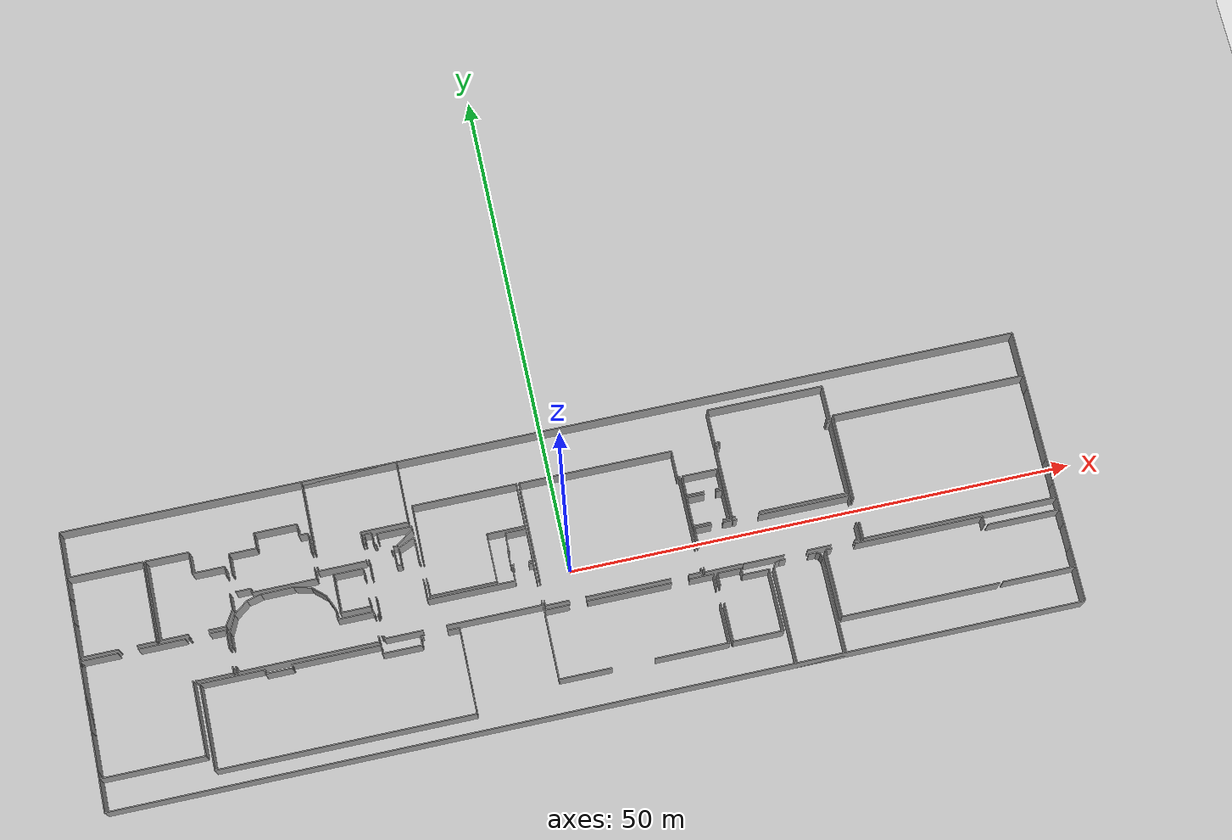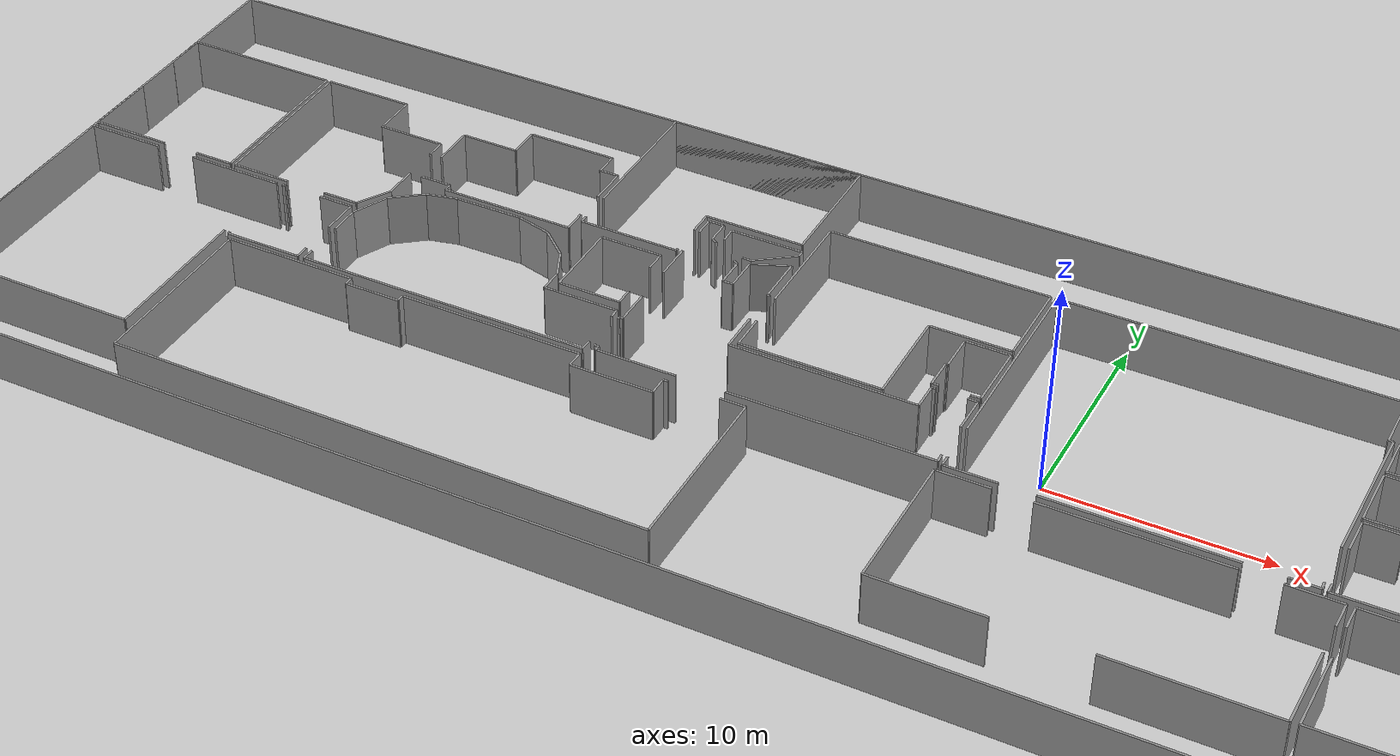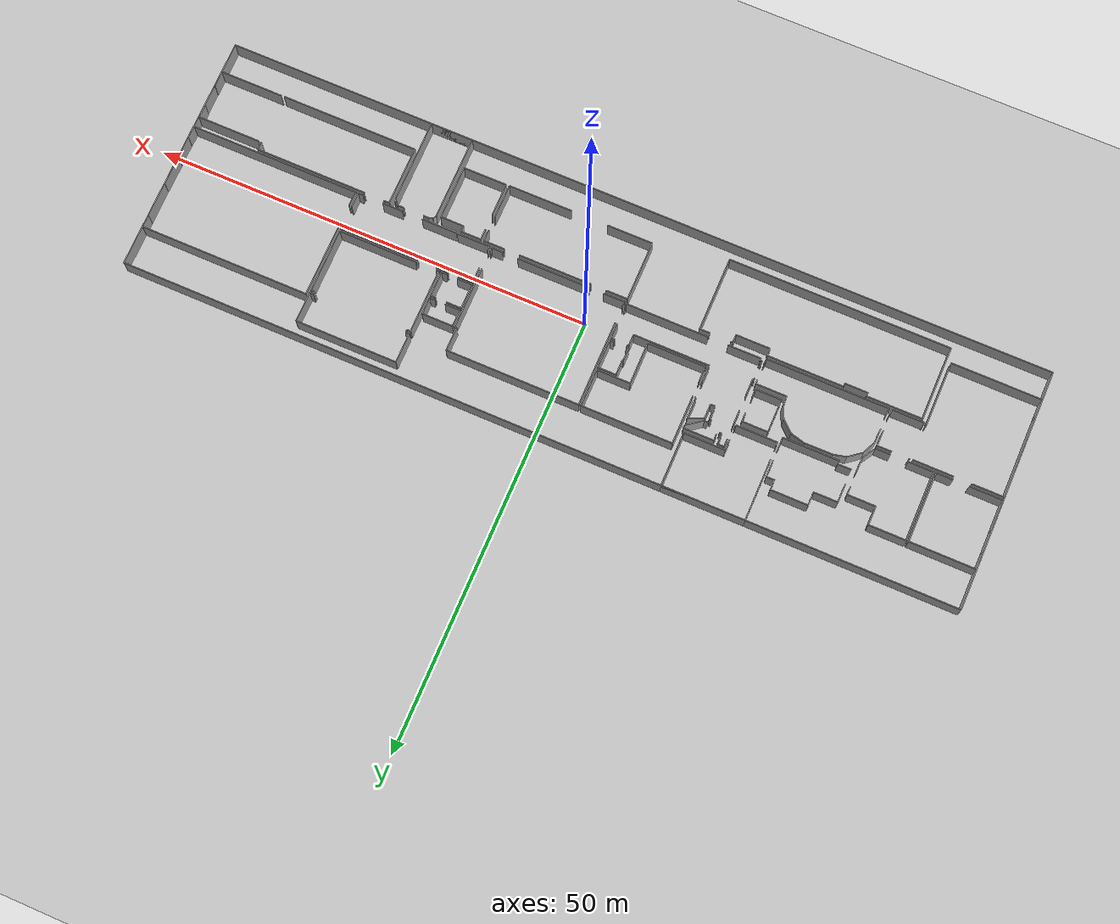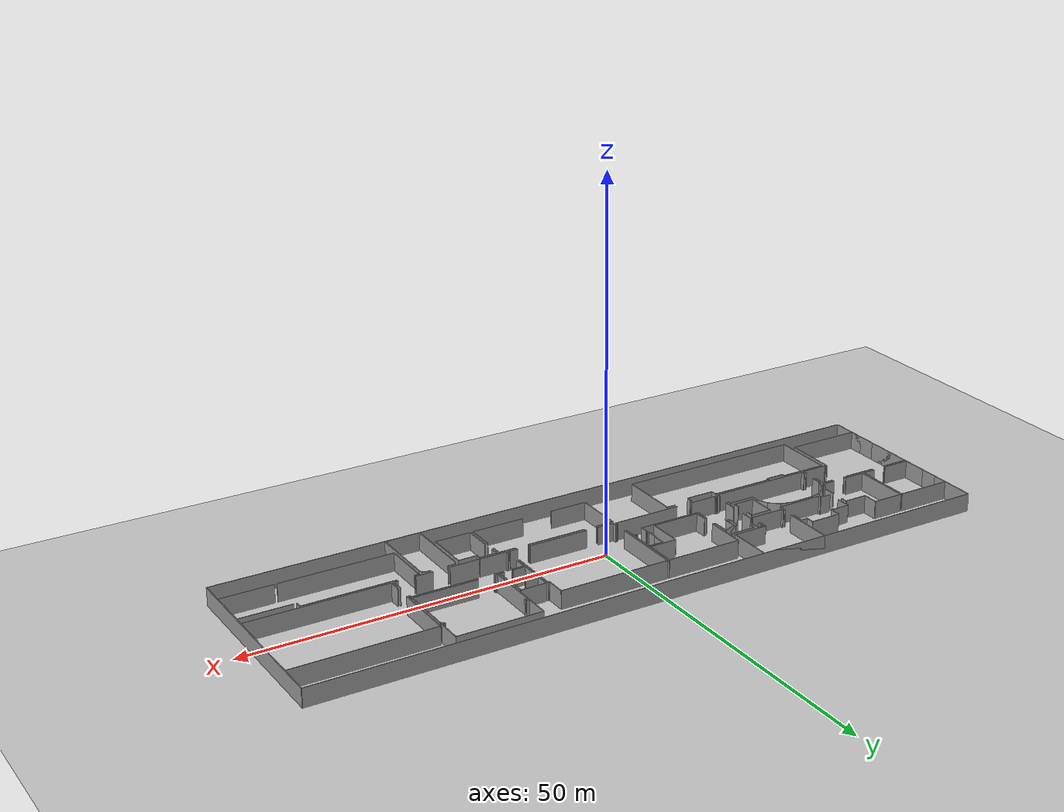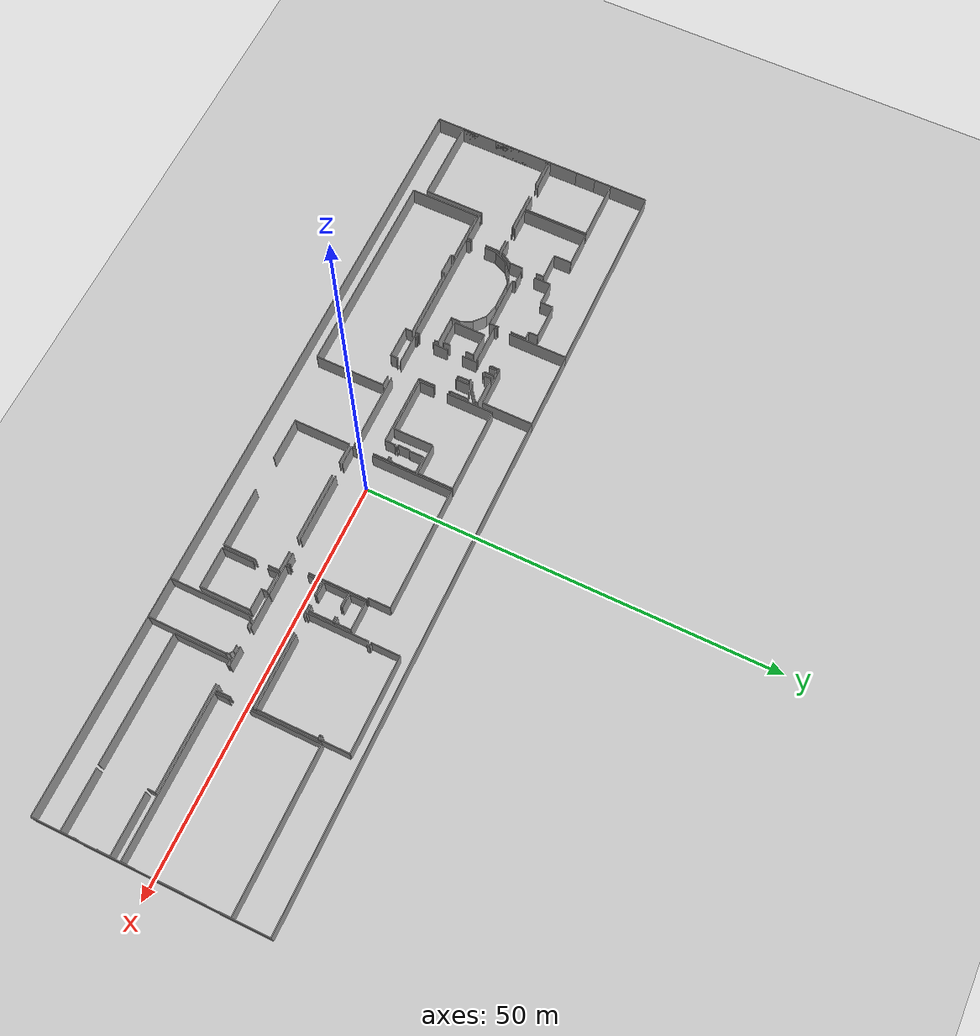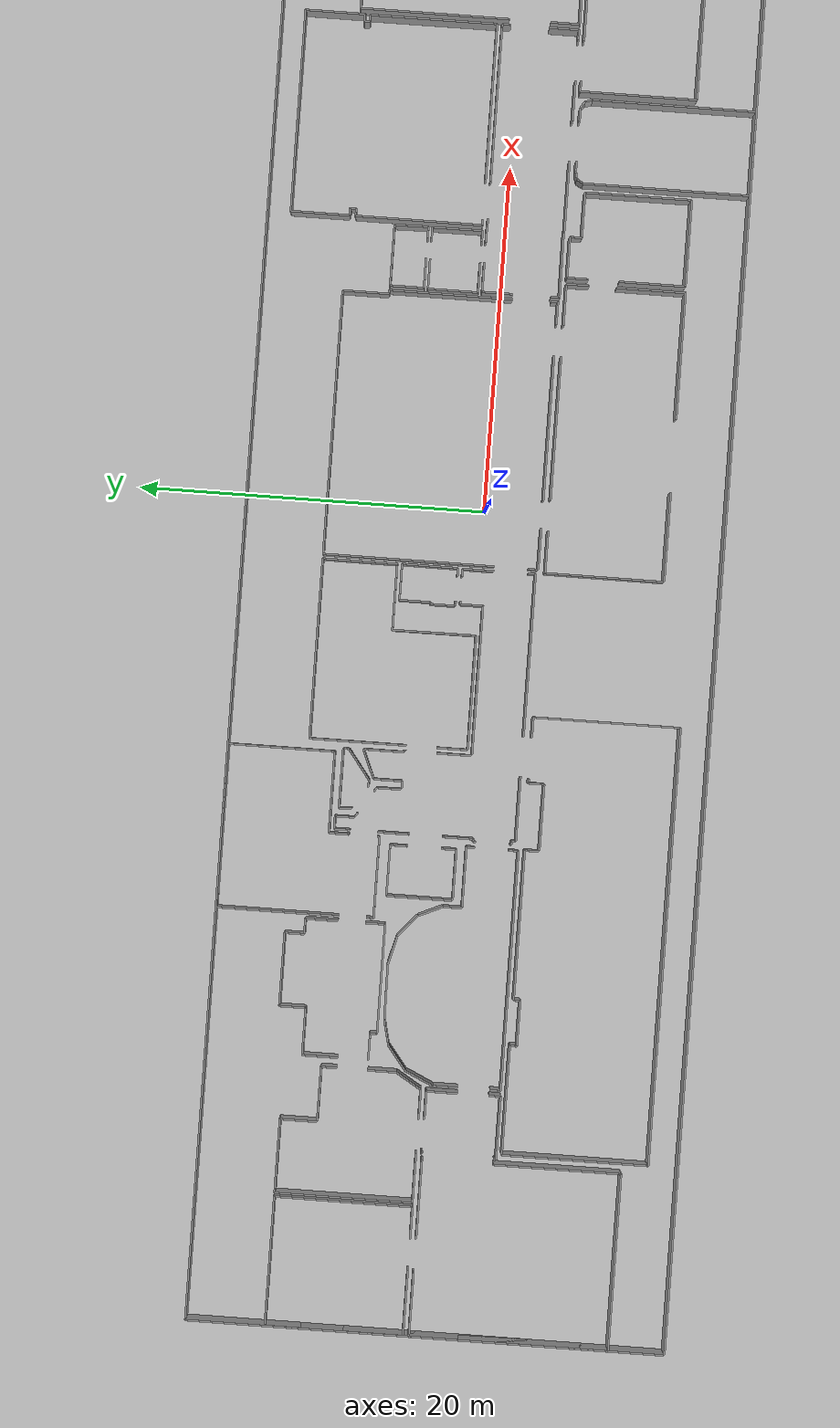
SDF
<sdf version="1.6">
  <world name="default">
    <light name="sun" type="directional">
      <cast_shadows>1</cast_shadows>
      <pose frame="">0 0 10 0 -0 0</pose>
      <diffuse>0.8 0.8 0.8 1</diffuse>
      <specular>0.1 0.1 0.1 1</specular>
      <attenuation>
        <range>1000</range>
        <constant>0.9</constant>
        <linear>0.01</linear>
        <quadratic>0.001</quadratic>
      </attenuation>
      <direction>-0.5 0.5 -1</direction>
    </light>
    <model name="ground_plane">
      <static>1</static>
      <link name="link">
        <collision name="collision">
          <geometry>
            <plane>
              <normal>0 0 1</normal>
              <size>100 100</size>
            </plane>
          </geometry>
          <surface>
            <friction>
              <ode>
                <mu>100</mu>
                <mu2>50</mu2>
              </ode>
              <torsional>
                <ode />
              </torsional>
            </friction>
            <contact>
              <ode />
            </contact>
            <bounce />
          </surface>
          <max_contacts>10</max_contacts>
        </collision>
        <visual name="visual">
          <cast_shadows>0</cast_shadows>
          <geometry>
            <plane>
              <normal>0 0 1</normal>
              <size>100 100</size>
            </plane>
          </geometry>
          <material>
            <script>
              <uri>file://media/materials/scripts/gazebo.material</uri>
              <name>Gazebo/Grey</name>
            </script>
          </material>
        </visual>
        <self_collide>0</self_collide>
        <kinematic>0</kinematic>
        <gravity>1</gravity>
      </link>
    </model>
    <gravity>0 0 -9.8</gravity>
    <magnetic_field>6e-06 2.3e-05 -4.2e-05</magnetic_field>
    <atmosphere type="adiabatic" />
    <physics default="0" name="default_physics" type="ode">
      <max_step_size>0.001</max_step_size>
      <real_time_factor>1</real_time_factor>
      <real_time_update_rate>1000</real_time_update_rate>
    </physics>
    <scene>
      <ambient>0.4 0.4 0.4 1</ambient>
      <background>0.7 0.7 0.7 1</background>
      <shadows>1</shadows>
    </scene>
    <spherical_coordinates>
      <surface_model>EARTH_WGS84</surface_model>
      <latitude_deg>0</latitude_deg>
      <longitude_deg>0</longitude_deg>
      <elevation>0</elevation>
      <heading_deg>0</heading_deg>
    </spherical_coordinates>
  <model name="0510032271_A_40_1_105">
		<static>1</static>
		<link name="Wall_0">
			<collision name="Wall_0_Collision">
				<geometry>
					<box>
						<size>1.86958950014 0.1 2.5</size>
					</box>
				</geometry>
				<pose frame="">0.93479475007 0 1.25 0 0 0</pose>
			</collision>
			<visual name="Wall_0_Visual">
				<pose frame="">0.93479475007 0 1.25 0 0 0</pose>
				<geometry>
					<box>
						<size>1.86958950014 0.1 2.5</size>
					</box>
				</geometry>
				<material>
					<script>
						<uri>file://media/materials/scripts/gazebo.material</uri>
						<name>Gazebo/Grey</name>
					</script>
					<ambient>1 1 1 1</ambient>
				</material>
			</visual>
			<pose frame="">7.43367774365 -12.5325581986 0 0 0 3.14159265359</pose>
		</link>
		<link name="Wall_1">
			<collision name="Wall_1_Collision">
				<geometry>
					<box>
						<size>3.76126526364 0.1 2.5</size>
					</box>
				</geometry>
				<pose frame="">1.88063263182 0 1.25 0 0 0</pose>
			</collision>
			<visual name="Wall_1_Visual">
				<pose frame="">1.88063263182 0 1.25 0 0 0</pose>
				<geometry>
					<box>
						<size>3.76126526364 0.1 2.5</size>
					</box>
				</geometry>
				<material>
					<script>
						<uri>file://media/materials/scripts/gazebo.material</uri>
						<name>Gazebo/Grey</name>
					</script>
					<ambient>1 1 1 1</ambient>
				</material>
			</visual>
			<pose frame="">3.76875428397 -12.5325581986 0 0 0 3.14159265359</pose>
		</link>
		<link name="Wall_2">
			<collision name="Wall_2_Collision">
				<geometry>
					<box>
						<size>3.45370769973 0.1 2.5</size>
					</box>
				</geometry>
				<pose frame="">1.72685384986 0 1.25 0 0 0</pose>
			</collision>
			<visual name="Wall_2_Visual">
				<pose frame="">1.72685384986 0 1.25 0 0 0</pose>
				<geometry>
					<box>
						<size>3.45370769973 0.1 2.5</size>
					</box>
				</geometry>
				<material>
					<script>
						<uri>file://media/materials/scripts/gazebo.material</uri>
						<name>Gazebo/Grey</name>
					</script>
					<ambient>1 1 1 1</ambient>
				</material>
			</visual>
			<pose frame="">0.0074890203346 -12.5325581986 0 0 0 1.57079632679</pose>
		</link>
		<link name="Wall_3">
			<collision name="Wall_3_Collision">
				<geometry>
					<box>
						<size>2.05668807596 0.1 2.5</size>
					</box>
				</geometry>
				<pose frame="">1.02834403798 0 1.25 0 0 0</pose>
			</collision>
			<visual name="Wall_3_Visual">
				<pose frame="">1.02834403798 0 1.25 0 0 0</pose>
				<geometry>
					<box>
						<size>2.05668807596 0.1 2.5</size>
					</box>
				</geometry>
				<material>
					<script>
						<uri>file://media/materials/scripts/gazebo.material</uri>
						<name>Gazebo/Grey</name>
					</script>
					<ambient>1 1 1 1</ambient>
				</material>
			</visual>
			<pose frame="">0.0074890203346 -6.63095630982 0 0 0 1.57079632679</pose>
		</link>
		<link name="Wall_4">
			<collision name="Wall_4_Collision">
				<geometry>
					<box>
						<size>7.446497931 0.1 2.5</size>
					</box>
				</geometry>
				<pose frame="">3.7232489655 0 1.25 0 0 0</pose>
			</collision>
			<visual name="Wall_4_Visual">
				<pose frame="">3.7232489655 0 1.25 0 0 0</pose>
				<geometry>
					<box>
						<size>7.446497931 0.1 2.5</size>
					</box>
				</geometry>
				<material>
					<script>
						<uri>file://media/materials/scripts/gazebo.material</uri>
						<name>Gazebo/Grey</name>
					</script>
					<ambient>1 1 1 1</ambient>
				</material>
			</visual>
			<pose frame="">0.0074890203346 -4.57426823386 0 0 0 0.0</pose>
		</link>
		<link name="Wall_5">
			<collision name="Wall_5_Collision">
				<geometry>
					<box>
						<size>7.95831587878 0.1 2.5</size>
					</box>
				</geometry>
				<pose frame="">3.97915793939 0 1.25 0 0 0</pose>
			</collision>
			<visual name="Wall_5_Visual">
				<pose frame="">3.97915793939 0 1.25 0 0 0</pose>
				<geometry>
					<box>
						<size>7.95831587878 0.1 2.5</size>
					</box>
				</geometry>
				<material>
					<script>
						<uri>file://media/materials/scripts/gazebo.material</uri>
						<name>Gazebo/Grey</name>
					</script>
					<ambient>1 1 1 1</ambient>
				</material>
			</visual>
			<pose frame="">7.45398695133 -4.57426823386 0 0 0 -1.57334827749</pose>
		</link>
		<link name="Wall_6">
			<collision name="Wall_6_Collision">
				<geometry>
					<box>
						<size>10.1986494377 0.1 2.5</size>
					</box>
				</geometry>
				<pose frame="">5.09932471884 0 1.25 0 0 0</pose>
			</collision>
			<visual name="Wall_6_Visual">
				<pose frame="">5.09932471884 0 1.25 0 0 0</pose>
				<geometry>
					<box>
						<size>10.1986494377 0.1 2.5</size>
					</box>
				</geometry>
				<material>
					<script>
						<uri>file://media/materials/scripts/gazebo.material</uri>
						<name>Gazebo/Grey</name>
					</script>
					<ambient>1 1 1 1</ambient>
				</material>
			</visual>
			<pose frame="">10.1986494377 -24.3393160874 0 0 0 3.14159265359</pose>
		</link>
		<link name="Wall_7">
			<collision name="Wall_7_Collision">
				<geometry>
					<box>
						<size>2.03904445178 0.1 2.5</size>
					</box>
				</geometry>
				<pose frame="">1.01952222589 0 1.25 0 0 0</pose>
			</collision>
			<visual name="Wall_7_Visual">
				<pose frame="">1.01952222589 0 1.25 0 0 0</pose>
				<geometry>
					<box>
						<size>2.03904445178 0.1 2.5</size>
					</box>
				</geometry>
				<material>
					<script>
						<uri>file://media/materials/scripts/gazebo.material</uri>
						<name>Gazebo/Grey</name>
					</script>
					<ambient>1 1 1 1</ambient>
				</material>
			</visual>
			<pose frame="">0.0 -24.3393160874 0 0 0 1.57079632679</pose>
		</link>
		<link name="Wall_8">
			<collision name="Wall_8_Collision">
				<geometry>
					<box>
						<size>4.1432053007 0.1 2.5</size>
					</box>
				</geometry>
				<pose frame="">2.07160265035 0 1.25 0 0 0</pose>
			</collision>
			<visual name="Wall_8_Visual">
				<pose frame="">2.07160265035 0 1.25 0 0 0</pose>
				<geometry>
					<box>
						<size>4.1432053007 0.1 2.5</size>
					</box>
				</geometry>
				<material>
					<script>
						<uri>file://media/materials/scripts/gazebo.material</uri>
						<name>Gazebo/Grey</name>
					</script>
					<ambient>1 1 1 1</ambient>
				</material>
			</visual>
			<pose frame="">0.0 -19.8389225965 0 0 0 1.57079632679</pose>
		</link>
		<link name="Wall_9">
			<collision name="Wall_9_Collision">
				<geometry>
					<box>
						<size>0.367215861491 0.1 2.5</size>
					</box>
				</geometry>
				<pose frame="">0.183607930746 0 1.25 0 0 0</pose>
			</collision>
			<visual name="Wall_9_Visual">
				<pose frame="">0.183607930746 0 1.25 0 0 0</pose>
				<geometry>
					<box>
						<size>0.367215861491 0.1 2.5</size>
					</box>
				</geometry>
				<material>
					<script>
						<uri>file://media/materials/scripts/gazebo.material</uri>
						<name>Gazebo/Grey</name>
					</script>
					<ambient>1 1 1 1</ambient>
				</material>
			</visual>
			<pose frame="">0.0 -13.2419842096 0 0 0 1.57079632679</pose>
		</link>
		<link name="Wall_10">
			<collision name="Wall_10_Collision">
				<geometry>
					<box>
						<size>3.64892995862 0.1 2.5</size>
					</box>
				</geometry>
				<pose frame="">1.82446497931 0 1.25 0 0 0</pose>
			</collision>
			<visual name="Wall_10_Visual">
				<pose frame="">1.82446497931 0 1.25 0 0 0</pose>
				<geometry>
					<box>
						<size>3.64892995862 0.1 2.5</size>
					</box>
				</geometry>
				<material>
					<script>
						<uri>file://media/materials/scripts/gazebo.material</uri>
						<name>Gazebo/Grey</name>
					</script>
					<ambient>1 1 1 1</ambient>
				</material>
			</visual>
			<pose frame="">0.0 -12.8747683481 0 0 0 0.0</pose>
		</link>
		<link name="Wall_11">
			<collision name="Wall_11_Collision">
				<geometry>
					<box>
						<size>4.58772308395 0.1 2.5</size>
					</box>
				</geometry>
				<pose frame="">2.29386154198 0 1.25 0 0 0</pose>
			</collision>
			<visual name="Wall_11_Visual">
				<pose frame="">2.29386154198 0 1.25 0 0 0</pose>
				<geometry>
					<box>
						<size>4.58772308395 0.1 2.5</size>
					</box>
				</geometry>
				<material>
					<script>
						<uri>file://media/materials/scripts/gazebo.material</uri>
						<name>Gazebo/Grey</name>
					</script>
					<ambient>1 1 1 1</ambient>
				</material>
			</visual>
			<pose frame="">5.60089868244 -12.8747683481 0 0 0 0.0</pose>
		</link>
		<link name="Wall_12">
			<collision name="Wall_12_Collision">
				<geometry>
					<box>
						<size>7.36450633191 0.1 2.5</size>
					</box>
				</geometry>
				<pose frame="">3.68225316596 0 1.25 0 0 0</pose>
			</collision>
			<visual name="Wall_12_Visual">
				<pose frame="">3.68225316596 0 1.25 0 0 0</pose>
				<geometry>
					<box>
						<size>7.36450633191 0.1 2.5</size>
					</box>
				</geometry>
				<material>
					<script>
						<uri>file://media/materials/scripts/gazebo.material</uri>
						<name>Gazebo/Grey</name>
					</script>
					<ambient>1 1 1 1</ambient>
				</material>
			</visual>
			<pose frame="">10.1886217664 -16.9748165825 0 0 0 -1.56943470472</pose>
		</link>
		<link name="Wall_13">
			<collision name="Wall_13_Collision">
				<geometry>
					<box>
						<size>3.63839455713 0.1 2.5</size>
					</box>
				</geometry>
				<pose frame="">1.81919727857 0 1.25 0 0 0</pose>
			</collision>
			<visual name="Wall_13_Visual">
				<pose frame="">1.81919727857 0 1.25 0 0 0</pose>
				<geometry>
					<box>
						<size>3.63839455713 0.1 2.5</size>
					</box>
				</geometry>
				<material>
					<script>
						<uri>file://media/materials/scripts/gazebo.material</uri>
						<name>Gazebo/Grey</name>
					</script>
					<ambient>1 1 1 1</ambient>
				</material>
			</visual>
			<pose frame="">14.1099489731 -17.11368079 0 0 0 3.14159265359</pose>
		</link>
		<link name="Wall_14">
			<collision name="Wall_14_Collision">
				<geometry>
					<box>
						<size>0.124393897083 0.1 2.5</size>
					</box>
				</geometry>
				<pose frame="">0.0621969485415 0 1.25 0 0 0</pose>
			</collision>
			<visual name="Wall_14_Visual">
				<pose frame="">0.0621969485415 0 1.25 0 0 0</pose>
				<geometry>
					<box>
						<size>0.124393897083 0.1 2.5</size>
					</box>
				</geometry>
				<material>
					<script>
						<uri>file://media/materials/scripts/gazebo.material</uri>
						<name>Gazebo/Grey</name>
					</script>
					<ambient>1 1 1 1</ambient>
				</material>
			</visual>
			<pose frame="">10.471554416 -17.11368079 0 0 0 1.57079632679</pose>
		</link>
		<link name="Wall_15">
			<collision name="Wall_15_Collision">
				<geometry>
					<box>
						<size>0.139371937752 0.1 2.5</size>
					</box>
				</geometry>
				<pose frame="">0.0696859688761 0 1.25 0 0 0</pose>
			</collision>
			<visual name="Wall_15_Visual">
				<pose frame="">0.0696859688761 0 1.25 0 0 0</pose>
				<geometry>
					<box>
						<size>0.139371937752 0.1 2.5</size>
					</box>
				</geometry>
				<material>
					<script>
						<uri>file://media/materials/scripts/gazebo.material</uri>
						<name>Gazebo/Grey</name>
					</script>
					<ambient>1 1 1 1</ambient>
				</material>
			</visual>
			<pose frame="">10.471554416 -12.8380848417 0 0 0 0.0</pose>
		</link>
		<link name="Wall_16">
			<collision name="Wall_16_Collision">
				<geometry>
					<box>
						<size>1.63590667919 0.1 2.5</size>
					</box>
				</geometry>
				<pose frame="">0.817953339595 0 1.25 0 0 0</pose>
			</collision>
			<visual name="Wall_16_Visual">
				<pose frame="">0.817953339595 0 1.25 0 0 0</pose>
				<geometry>
					<box>
						<size>1.63590667919 0.1 2.5</size>
					</box>
				</geometry>
				<material>
					<script>
						<uri>file://media/materials/scripts/gazebo.material</uri>
						<name>Gazebo/Grey</name>
					</script>
					<ambient>1 1 1 1</ambient>
				</material>
			</visual>
			<pose frame="">12.4829275723 -12.8380848417 0 0 0 0.0</pose>
		</link>
		<link name="Wall_17">
			<collision name="Wall_17_Collision">
				<geometry>
					<box>
						<size>1.80866187708 0.1 2.5</size>
					</box>
				</geometry>
				<pose frame="">0.904330938539 0 1.25 0 0 0</pose>
			</collision>
			<visual name="Wall_17_Visual">
				<pose frame="">0.904330938539 0 1.25 0 0 0</pose>
				<geometry>
					<box>
						<size>1.80866187708 0.1 2.5</size>
					</box>
				</geometry>
				<material>
					<script>
						<uri>file://media/materials/scripts/gazebo.material</uri>
						<name>Gazebo/Grey</name>
					</script>
					<ambient>1 1 1 1</ambient>
				</material>
			</visual>
			<pose frame="">14.1188342515 -12.8380848417 0 0 0 -1.57079632679</pose>
		</link>
		<link name="Wall_18">
			<collision name="Wall_18_Collision">
				<geometry>
					<box>
						<size>0.661885946992 0.1 2.5</size>
					</box>
				</geometry>
				<pose frame="">0.330942973496 0 1.25 0 0 0</pose>
			</collision>
			<visual name="Wall_18_Visual">
				<pose frame="">0.330942973496 0 1.25 0 0 0</pose>
				<geometry>
					<box>
						<size>0.661885946992 0.1 2.5</size>
					</box>
				</geometry>
				<material>
					<script>
						<uri>file://media/materials/scripts/gazebo.material</uri>
						<name>Gazebo/Grey</name>
					</script>
					<ambient>1 1 1 1</ambient>
				</material>
			</visual>
			<pose frame="">14.1188342515 -16.4518544845 0 0 0 -1.58422091345</pose>
		</link>
		<link name="Wall_19">
			<collision name="Wall_19_Collision">
				<geometry>
					<box>
						<size>1.71079688254 0.1 2.5</size>
					</box>
				</geometry>
				<pose frame="">0.855398441268 0 1.25 0 0 0</pose>
			</collision>
			<visual name="Wall_19_Visual">
				<pose frame="">0.855398441268 0 1.25 0 0 0</pose>
				<geometry>
					<box>
						<size>1.71079688254 0.1 2.5</size>
					</box>
				</geometry>
				<material>
					<script>
						<uri>file://media/materials/scripts/gazebo.material</uri>
						<name>Gazebo/Grey</name>
					</script>
					<ambient>1 1 1 1</ambient>
				</material>
			</visual>
			<pose frame="">14.1833159859 -12.509964205 0 0 0 3.14159265359</pose>
		</link>
		<link name="Wall_20">
			<collision name="Wall_20_Collision">
				<geometry>
					<box>
						<size>2.85598233099 0.1 2.5</size>
					</box>
				</geometry>
				<pose frame="">1.42799116549 0 1.25 0 0 0</pose>
			</collision>
			<visual name="Wall_20_Visual">
				<pose frame="">1.42799116549 0 1.25 0 0 0</pose>
				<geometry>
					<box>
						<size>2.85598233099 0.1 2.5</size>
					</box>
				</geometry>
				<material>
					<script>
						<uri>file://media/materials/scripts/gazebo.material</uri>
						<name>Gazebo/Grey</name>
					</script>
					<ambient>1 1 1 1</ambient>
				</material>
			</visual>
			<pose frame="">10.5133152243 -12.509964205 0 0 0 3.14159265359</pose>
		</link>
		<link name="Wall_21">
			<collision name="Wall_21_Collision">
				<geometry>
					<box>
						<size>7.93696529664 0.1 2.5</size>
					</box>
				</geometry>
				<pose frame="">3.96848264832 0 1.25 0 0 0</pose>
			</collision>
			<visual name="Wall_21_Visual">
				<pose frame="">3.96848264832 0 1.25 0 0 0</pose>
				<geometry>
					<box>
						<size>7.93696529664 0.1 2.5</size>
					</box>
				</geometry>
				<material>
					<script>
						<uri>file://media/materials/scripts/gazebo.material</uri>
						<name>Gazebo/Grey</name>
					</script>
					<ambient>1 1 1 1</ambient>
				</material>
			</visual>
			<pose frame="">7.6573328933 -12.509964205 0 0 0 1.57079632679</pose>
		</link>
		<link name="Wall_22">
			<collision name="Wall_22_Collision">
				<geometry>
					<box>
						<size>4.24932091087 0.1 2.5</size>
					</box>
				</geometry>
				<pose frame="">2.12466045543 0 1.25 0 0 0</pose>
			</collision>
			<visual name="Wall_22_Visual">
				<pose frame="">2.12466045543 0 1.25 0 0 0</pose>
				<geometry>
					<box>
						<size>4.24932091087 0.1 2.5</size>
					</box>
				</geometry>
				<material>
					<script>
						<uri>file://media/materials/scripts/gazebo.material</uri>
						<name>Gazebo/Grey</name>
					</script>
					<ambient>1 1 1 1</ambient>
				</material>
			</visual>
			<pose frame="">7.6573328933 -4.57299890838 0 0 0 0.0</pose>
		</link>
		<link name="Wall_23">
			<collision name="Wall_23_Collision">
				<geometry>
					<box>
						<size>2.13398999772 0.1 2.5</size>
					</box>
				</geometry>
				<pose frame="">1.06699499886 0 1.25 0 0 0</pose>
			</collision>
			<visual name="Wall_23_Visual">
				<pose frame="">1.06699499886 0 1.25 0 0 0</pose>
				<geometry>
					<box>
						<size>2.13398999772 0.1 2.5</size>
					</box>
				</geometry>
				<material>
					<script>
						<uri>file://media/materials/scripts/gazebo.material</uri>
						<name>Gazebo/Grey</name>
					</script>
					<ambient>1 1 1 1</ambient>
				</material>
			</visual>
			<pose frame="">11.9066538042 -4.57299890838 0 0 0 -1.57079632679</pose>
		</link>
		<link name="Wall_24">
			<collision name="Wall_24_Collision">
				<geometry>
					<box>
						<size>3.1635398949 0.1 2.5</size>
					</box>
				</geometry>
				<pose frame="">1.58176994745 0 1.25 0 0 0</pose>
			</collision>
			<visual name="Wall_24_Visual">
				<pose frame="">1.58176994745 0 1.25 0 0 0</pose>
				<geometry>
					<box>
						<size>3.1635398949 0.1 2.5</size>
					</box>
				</geometry>
				<material>
					<script>
						<uri>file://media/materials/scripts/gazebo.material</uri>
						<name>Gazebo/Grey</name>
					</script>
					<ambient>1 1 1 1</ambient>
				</material>
			</visual>
			<pose frame="">11.9066538042 -6.7069889061 0 0 0 0.0</pose>
		</link>
		<link name="Wall_25">
			<collision name="Wall_25_Collision">
				<geometry>
					<box>
						<size>0.918103120002 0.1 2.5</size>
					</box>
				</geometry>
				<pose frame="">0.459051560001 0 1.25 0 0 0</pose>
			</collision>
			<visual name="Wall_25_Visual">
				<pose frame="">0.459051560001 0 1.25 0 0 0</pose>
				<geometry>
					<box>
						<size>0.918103120002 0.1 2.5</size>
					</box>
				</geometry>
				<material>
					<script>
						<uri>file://media/materials/scripts/gazebo.material</uri>
						<name>Gazebo/Grey</name>
					</script>
					<ambient>1 1 1 1</ambient>
				</material>
			</visual>
			<pose frame="">15.0701936991 -6.7069889061 0 0 0 -1.57079632679</pose>
		</link>
		<link name="Wall_26">
			<collision name="Wall_26_Collision">
				<geometry>
					<box>
						<size>1.648599934 0.1 2.5</size>
					</box>
				</geometry>
				<pose frame="">0.824299966998 0 1.25 0 0 0</pose>
			</collision>
			<visual name="Wall_26_Visual">
				<pose frame="">0.824299966998 0 1.25 0 0 0</pose>
				<geometry>
					<box>
						<size>1.648599934 0.1 2.5</size>
					</box>
				</geometry>
				<material>
					<script>
						<uri>file://media/materials/scripts/gazebo.material</uri>
						<name>Gazebo/Grey</name>
					</script>
					<ambient>1 1 1 1</ambient>
				</material>
			</visual>
			<pose frame="">15.0701936991 -9.38843898352 0 0 0 -1.57079632679</pose>
		</link>
		<link name="Wall_27">
			<collision name="Wall_27_Collision">
				<geometry>
					<box>
						<size>1.71931991808 0.1 2.5</size>
					</box>
				</geometry>
				<pose frame="">0.85965995904 0 1.25 0 0 0</pose>
			</collision>
			<visual name="Wall_27_Visual">
				<pose frame="">0.85965995904 0 1.25 0 0 0</pose>
				<geometry>
					<box>
						<size>1.71931991808 0.1 2.5</size>
					</box>
				</geometry>
				<material>
					<script>
						<uri>file://media/materials/scripts/gazebo.material</uri>
						<name>Gazebo/Grey</name>
					</script>
					<ambient>1 1 1 1</ambient>
				</material>
			</visual>
			<pose frame="">15.0701936991 -11.0370389175 0 0 0 -2.11277316238</pose>
		</link>
		<link name="Wall_28">
			<collision name="Wall_28_Collision">
				<geometry>
					<box>
						<size>6.33456881013 0.1 2.5</size>
					</box>
				</geometry>
				<pose frame="">3.16728440507 0 1.25 0 0 0</pose>
			</collision>
			<visual name="Wall_28_Visual">
				<pose frame="">3.16728440507 0 1.25 0 0 0</pose>
				<geometry>
					<box>
						<size>6.33456881013 0.1 2.5</size>
					</box>
				</geometry>
				<material>
					<script>
						<uri>file://media/materials/scripts/gazebo.material</uri>
						<name>Gazebo/Grey</name>
					</script>
					<ambient>1 1 1 1</ambient>
				</material>
			</visual>
			<pose frame="">23.5009266076 -9.76542865121 0 0 0 3.14159265359</pose>
		</link>
		<link name="Wall_29">
			<collision name="Wall_29_Collision">
				<geometry>
					<box>
						<size>0.393490898936 0.1 2.5</size>
					</box>
				</geometry>
				<pose frame="">0.196745449468 0 1.25 0 0 0</pose>
			</collision>
			<visual name="Wall_29_Visual">
				<pose frame="">0.196745449468 0 1.25 0 0 0</pose>
				<geometry>
					<box>
						<size>0.393490898936 0.1 2.5</size>
					</box>
				</geometry>
				<material>
					<script>
						<uri>file://media/materials/scripts/gazebo.material</uri>
						<name>Gazebo/Grey</name>
					</script>
					<ambient>1 1 1 1</ambient>
				</material>
			</visual>
			<pose frame="">17.1663577975 -9.76542865121 0 0 0 1.57079632679</pose>
		</link>
		<link name="Wall_30">
			<collision name="Wall_30_Collision">
				<geometry>
					<box>
						<size>1.50681627783 0.1 2.5</size>
					</box>
				</geometry>
				<pose frame="">0.753408138915 0 1.25 0 0 0</pose>
			</collision>
			<visual name="Wall_30_Visual">
				<pose frame="">0.753408138915 0 1.25 0 0 0</pose>
				<geometry>
					<box>
						<size>1.50681627783 0.1 2.5</size>
					</box>
				</geometry>
				<material>
					<script>
						<uri>file://media/materials/scripts/gazebo.material</uri>
						<name>Gazebo/Grey</name>
					</script>
					<ambient>1 1 1 1</ambient>
				</material>
			</visual>
			<pose frame="">17.1663577975 -9.37193775228 0 0 0 3.14159265359</pose>
		</link>
		<link name="Wall_31">
			<collision name="Wall_31_Collision">
				<geometry>
					<box>
						<size>2.06125764769 0.1 2.5</size>
					</box>
				</geometry>
				<pose frame="">1.03062882384 0 1.25 0 0 0</pose>
			</collision>
			<visual name="Wall_31_Visual">
				<pose frame="">1.03062882384 0 1.25 0 0 0</pose>
				<geometry>
					<box>
						<size>2.06125764769 0.1 2.5</size>
					</box>
				</geometry>
				<material>
					<script>
						<uri>file://media/materials/scripts/gazebo.material</uri>
						<name>Gazebo/Grey</name>
					</script>
					<ambient>1 1 1 1</ambient>
				</material>
			</visual>
			<pose frame="">15.6595415196 -7.63308877662 0 0 0 1.57079632679</pose>
		</link>
		<link name="Wall_32">
			<collision name="Wall_32_Collision">
				<geometry>
					<box>
						<size>2.71876824655 0.1 2.5</size>
					</box>
				</geometry>
				<pose frame="">1.35938412328 0 1.25 0 0 0</pose>
			</collision>
			<visual name="Wall_32_Visual">
				<pose frame="">1.35938412328 0 1.25 0 0 0</pose>
				<geometry>
					<box>
						<size>2.71876824655 0.1 2.5</size>
					</box>
				</geometry>
				<material>
					<script>
						<uri>file://media/materials/scripts/gazebo.material</uri>
						<name>Gazebo/Grey</name>
					</script>
					<ambient>1 1 1 1</ambient>
				</material>
			</visual>
			<pose frame="">15.6595415196 -5.57183112894 0 0 0 0.0</pose>
		</link>
		<link name="Wall_33">
			<collision name="Wall_33_Collision">
				<geometry>
					<box>
						<size>1.52090579066 0.1 2.5</size>
					</box>
				</geometry>
				<pose frame="">0.760452895331 0 1.25 0 0 0</pose>
			</collision>
			<visual name="Wall_33_Visual">
				<pose frame="">0.760452895331 0 1.25 0 0 0</pose>
				<geometry>
					<box>
						<size>1.52090579066 0.1 2.5</size>
					</box>
				</geometry>
				<material>
					<script>
						<uri>file://media/materials/scripts/gazebo.material</uri>
						<name>Gazebo/Grey</name>
					</script>
					<ambient>1 1 1 1</ambient>
				</material>
			</visual>
			<pose frame="">18.3783097662 -5.57183112894 0 0 0 1.57079632679</pose>
		</link>
		<link name="Wall_34">
			<collision name="Wall_34_Collision">
				<geometry>
					<box>
						<size>4.21555685309 0.1 2.5</size>
					</box>
				</geometry>
				<pose frame="">2.10777842654 0 1.25 0 0 0</pose>
			</collision>
			<visual name="Wall_34_Visual">
				<pose frame="">2.10777842654 0 1.25 0 0 0</pose>
				<geometry>
					<box>
						<size>4.21555685309 0.1 2.5</size>
					</box>
				</geometry>
				<material>
					<script>
						<uri>file://media/materials/scripts/gazebo.material</uri>
						<name>Gazebo/Grey</name>
					</script>
					<ambient>1 1 1 1</ambient>
				</material>
			</visual>
			<pose frame="">18.3783097662 -4.05092533828 0 0 0 0.0</pose>
		</link>
		<link name="Wall_35">
			<collision name="Wall_35_Collision">
				<geometry>
					<box>
						<size>1.12969967759 0.1 2.5</size>
					</box>
				</geometry>
				<pose frame="">0.564849838796 0 1.25 0 0 0</pose>
			</collision>
			<visual name="Wall_35_Visual">
				<pose frame="">0.564849838796 0 1.25 0 0 0</pose>
				<geometry>
					<box>
						<size>1.12969967759 0.1 2.5</size>
					</box>
				</geometry>
				<material>
					<script>
						<uri>file://media/materials/scripts/gazebo.material</uri>
						<name>Gazebo/Grey</name>
					</script>
					<ambient>1 1 1 1</ambient>
				</material>
			</visual>
			<pose frame="">22.5938666193 -4.05092533828 0 0 0 -1.57079632679</pose>
		</link>
		<link name="Wall_36">
			<collision name="Wall_36_Collision">
				<geometry>
					<box>
						<size>0.89614378919 0.1 2.5</size>
					</box>
				</geometry>
				<pose frame="">0.448071894595 0 1.25 0 0 0</pose>
			</collision>
			<visual name="Wall_36_Visual">
				<pose frame="">0.448071894595 0 1.25 0 0 0</pose>
				<geometry>
					<box>
						<size>0.89614378919 0.1 2.5</size>
					</box>
				</geometry>
				<material>
					<script>
						<uri>file://media/materials/scripts/gazebo.material</uri>
						<name>Gazebo/Grey</name>
					</script>
					<ambient>1 1 1 1</ambient>
				</material>
			</visual>
			<pose frame="">22.5938666193 -5.18062501587 0 0 0 0.0</pose>
		</link>
		<link name="Wall_37">
			<collision name="Wall_37_Collision">
				<geometry>
					<box>
						<size>1.8819019573 0.1 2.5</size>
					</box>
				</geometry>
				<pose frame="">0.94095097865 0 1.25 0 0 0</pose>
			</collision>
			<visual name="Wall_37_Visual">
				<pose frame="">0.94095097865 0 1.25 0 0 0</pose>
				<geometry>
					<box>
						<size>1.8819019573 0.1 2.5</size>
					</box>
				</geometry>
				<material>
					<script>
						<uri>file://media/materials/scripts/gazebo.material</uri>
						<name>Gazebo/Grey</name>
					</script>
					<ambient>1 1 1 1</ambient>
				</material>
			</visual>
			<pose frame="">23.4900104085 -5.18062501587 0 0 0 -1.57079632679</pose>
		</link>
		<link name="Wall_38">
			<collision name="Wall_38_Collision">
				<geometry>
					<box>
						<size>1.1294985643 0.1 2.5</size>
					</box>
				</geometry>
				<pose frame="">0.564749282152 0 1.25 0 0 0</pose>
			</collision>
			<visual name="Wall_38_Visual">
				<pose frame="">0.564749282152 0 1.25 0 0 0</pose>
				<geometry>
					<box>
						<size>1.1294985643 0.1 2.5</size>
					</box>
				</geometry>
				<material>
					<script>
						<uri>file://media/materials/scripts/gazebo.material</uri>
						<name>Gazebo/Grey</name>
					</script>
					<ambient>1 1 1 1</ambient>
				</material>
			</visual>
			<pose frame="">23.4900104085 -8.63598283872 0 0 0 -1.56113153445</pose>
		</link>
		<link name="Wall_39">
			<collision name="Wall_39_Collision">
				<geometry>
					<box>
						<size>4.68838059455 0.1 2.5</size>
					</box>
				</geometry>
				<pose frame="">2.34419029728 0 1.25 0 0 0</pose>
			</collision>
			<visual name="Wall_39_Visual">
				<pose frame="">2.34419029728 0 1.25 0 0 0</pose>
				<geometry>
					<box>
						<size>4.68838059455 0.1 2.5</size>
					</box>
				</geometry>
				<material>
					<script>
						<uri>file://media/materials/scripts/gazebo.material</uri>
						<name>Gazebo/Grey</name>
					</script>
					<ambient>1 1 1 1</ambient>
				</material>
			</visual>
			<pose frame="">33.1790256658 -6.15229367114 0 0 0 3.14159265359</pose>
		</link>
		<link name="Wall_40">
			<collision name="Wall_40_Collision">
				<geometry>
					<box>
						<size>1.18897717753 0.1 2.5</size>
					</box>
				</geometry>
				<pose frame="">0.594488588764 0 1.25 0 0 0</pose>
			</collision>
			<visual name="Wall_40_Visual">
				<pose frame="">0.594488588764 0 1.25 0 0 0</pose>
				<geometry>
					<box>
						<size>1.18897717753 0.1 2.5</size>
					</box>
				</geometry>
				<material>
					<script>
						<uri>file://media/materials/scripts/gazebo.material</uri>
						<name>Gazebo/Grey</name>
					</script>
					<ambient>1 1 1 1</ambient>
				</material>
			</visual>
			<pose frame="">28.4906450712 -6.15229367114 0 0 0 -1.57079632679</pose>
		</link>
		<link name="Wall_41">
			<collision name="Wall_41_Collision">
				<geometry>
					<box>
						<size>0.130613591937 0.1 2.5</size>
					</box>
				</geometry>
				<pose frame="">0.0653067959686 0 1.25 0 0 0</pose>
			</collision>
			<visual name="Wall_41_Visual">
				<pose frame="">0.0653067959686 0 1.25 0 0 0</pose>
				<geometry>
					<box>
						<size>0.130613591937 0.1 2.5</size>
					</box>
				</geometry>
				<material>
					<script>
						<uri>file://media/materials/scripts/gazebo.material</uri>
						<name>Gazebo/Grey</name>
					</script>
					<ambient>1 1 1 1</ambient>
				</material>
			</visual>
			<pose frame="">28.4906450712 -8.94087481912 0 0 0 -1.57079632679</pose>
		</link>
		<link name="Wall_42">
			<collision name="Wall_42_Collision">
				<geometry>
					<box>
						<size>4.71478256455 0.1 2.5</size>
					</box>
				</geometry>
				<pose frame="">2.35739128227 0 1.25 0 0 0</pose>
			</collision>
			<visual name="Wall_42_Visual">
				<pose frame="">2.35739128227 0 1.25 0 0 0</pose>
				<geometry>
					<box>
						<size>4.71478256455 0.1 2.5</size>
					</box>
				</geometry>
				<material>
					<script>
						<uri>file://media/materials/scripts/gazebo.material</uri>
						<name>Gazebo/Grey</name>
					</script>
					<ambient>1 1 1 1</ambient>
				</material>
			</visual>
			<pose frame="">28.4906450712 -9.07148841106 0 0 0 3.14159265359</pose>
		</link>
		<link name="Wall_43">
			<collision name="Wall_43_Collision">
				<geometry>
					<box>
						<size>0.399202863598 0.1 2.5</size>
					</box>
				</geometry>
				<pose frame="">0.199601431799 0 1.25 0 0 0</pose>
			</collision>
			<visual name="Wall_43_Visual">
				<pose frame="">0.199601431799 0 1.25 0 0 0</pose>
				<geometry>
					<box>
						<size>0.399202863598 0.1 2.5</size>
					</box>
				</geometry>
				<material>
					<script>
						<uri>file://media/materials/scripts/gazebo.material</uri>
						<name>Gazebo/Grey</name>
					</script>
					<ambient>1 1 1 1</ambient>
				</material>
			</visual>
			<pose frame="">23.7758625067 -9.07148841106 0 0 0 1.57079632679</pose>
		</link>
		<link name="Wall_44">
			<collision name="Wall_44_Collision">
				<geometry>
					<box>
						<size>7.08994440354 0.1 2.5</size>
					</box>
				</geometry>
				<pose frame="">3.54497220177 0 1.25 0 0 0</pose>
			</collision>
			<visual name="Wall_44_Visual">
				<pose frame="">3.54497220177 0 1.25 0 0 0</pose>
				<geometry>
					<box>
						<size>7.08994440354 0.1 2.5</size>
					</box>
				</geometry>
				<material>
					<script>
						<uri>file://media/materials/scripts/gazebo.material</uri>
						<name>Gazebo/Grey</name>
					</script>
					<ambient>1 1 1 1</ambient>
				</material>
			</visual>
			<pose frame="">23.7758625067 -7.08994440354 0 0 0 1.57079632679</pose>
		</link>
		<link name="Wall_45">
			<collision name="Wall_45_Collision">
				<geometry>
					<box>
						<size>9.40519407987 0.1 2.5</size>
					</box>
				</geometry>
				<pose frame="">4.70259703993 0 1.25 0 0 0</pose>
			</collision>
			<visual name="Wall_45_Visual">
				<pose frame="">4.70259703993 0 1.25 0 0 0</pose>
				<geometry>
					<box>
						<size>9.40519407987 0.1 2.5</size>
					</box>
				</geometry>
				<material>
					<script>
						<uri>file://media/materials/scripts/gazebo.material</uri>
						<name>Gazebo/Grey</name>
					</script>
					<ambient>1 1 1 1</ambient>
				</material>
			</visual>
			<pose frame="">23.7758625067 -0.0 0 0 0 0.0</pose>
		</link>
		<link name="Wall_46">
			<collision name="Wall_46_Collision">
				<geometry>
					<box>
						<size>6.15229400635 0.1 2.5</size>
					</box>
				</geometry>
				<pose frame="">3.07614700318 0 1.25 0 0 0</pose>
			</collision>
			<visual name="Wall_46_Visual">
				<pose frame="">3.07614700318 0 1.25 0 0 0</pose>
				<geometry>
					<box>
						<size>6.15229400635 0.1 2.5</size>
					</box>
				</geometry>
				<material>
					<script>
						<uri>file://media/materials/scripts/gazebo.material</uri>
						<name>Gazebo/Grey</name>
					</script>
					<ambient>1 1 1 1</ambient>
				</material>
			</visual>
			<pose frame="">33.1810565865 -0.0 0 0 0 -1.57112643469</pose>
		</link>
		<link name="Wall_47">
			<collision name="Wall_47_Collision">
				<geometry>
					<box>
						<size>13.7921098728 0.1 2.5</size>
					</box>
				</geometry>
				<pose frame="">6.89605493641 0 1.25 0 0 0</pose>
			</collision>
			<visual name="Wall_47_Visual">
				<pose frame="">6.89605493641 0 1.25 0 0 0</pose>
				<geometry>
					<box>
						<size>13.7921098728 0.1 2.5</size>
					</box>
				</geometry>
				<material>
					<script>
						<uri>file://media/materials/scripts/gazebo.material</uri>
						<name>Gazebo/Grey</name>
					</script>
					<ambient>1 1 1 1</ambient>
				</material>
			</visual>
			<pose frame="">28.2327181336 -17.0886750781 0 0 0 3.14159265359</pose>
		</link>
		<link name="Wall_48">
			<collision name="Wall_48_Collision">
				<geometry>
					<box>
						<size>0.60737224239 0.1 2.5</size>
					</box>
				</geometry>
				<pose frame="">0.303686121195 0 1.25 0 0 0</pose>
			</collision>
			<visual name="Wall_48_Visual">
				<pose frame="">0.303686121195 0 1.25 0 0 0</pose>
				<geometry>
					<box>
						<size>0.60737224239 0.1 2.5</size>
					</box>
				</geometry>
				<material>
					<script>
						<uri>file://media/materials/scripts/gazebo.material</uri>
						<name>Gazebo/Grey</name>
					</script>
					<ambient>1 1 1 1</ambient>
				</material>
			</visual>
			<pose frame="">14.4406082608 -17.0886750781 0 0 0 1.57079632679</pose>
		</link>
		<link name="Wall_49">
			<collision name="Wall_49_Collision">
				<geometry>
					<box>
						<size>1.45693178645 0.1 2.5</size>
					</box>
				</geometry>
				<pose frame="">0.728465893224 0 1.25 0 0 0</pose>
			</collision>
			<visual name="Wall_49_Visual">
				<pose frame="">0.728465893224 0 1.25 0 0 0</pose>
				<geometry>
					<box>
						<size>1.45693178645 0.1 2.5</size>
					</box>
				</geometry>
				<material>
					<script>
						<uri>file://media/materials/scripts/gazebo.material</uri>
						<name>Gazebo/Grey</name>
					</script>
					<ambient>1 1 1 1</ambient>
				</material>
			</visual>
			<pose frame="">14.4406082608 -14.6401462263 0 0 0 1.57079632679</pose>
		</link>
		<link name="Wall_50">
			<collision name="Wall_50_Collision">
				<geometry>
					<box>
						<size>1.78620986174 0.1 2.5</size>
					</box>
				</geometry>
				<pose frame="">0.89310493087 0 1.25 0 0 0</pose>
			</collision>
			<visual name="Wall_50_Visual">
				<pose frame="">0.89310493087 0 1.25 0 0 0</pose>
				<geometry>
					<box>
						<size>1.78620986174 0.1 2.5</size>
					</box>
				</geometry>
				<material>
					<script>
						<uri>file://media/materials/scripts/gazebo.material</uri>
						<name>Gazebo/Grey</name>
					</script>
					<ambient>1 1 1 1</ambient>
				</material>
			</visual>
			<pose frame="">14.4406082608 -13.1832144398 0 0 0 1.13925215173</pose>
		</link>
		<link name="Wall_51">
			<collision name="Wall_51_Collision">
				<geometry>
					<box>
						<size>1.77744013238 0.1 2.5</size>
					</box>
				</geometry>
				<pose frame="">0.888720066191 0 1.25 0 0 0</pose>
			</collision>
			<visual name="Wall_51_Visual">
				<pose frame="">0.888720066191 0 1.25 0 0 0</pose>
				<geometry>
					<box>
						<size>1.77744013238 0.1 2.5</size>
					</box>
				</geometry>
				<material>
					<script>
						<uri>file://media/materials/scripts/gazebo.material</uri>
						<name>Gazebo/Grey</name>
					</script>
					<ambient>1 1 1 1</ambient>
				</material>
			</visual>
			<pose frame="">15.1877332386 -11.5607626107 0 0 0 0.662126727762</pose>
		</link>
		<link name="Wall_52">
			<collision name="Wall_52_Collision">
				<geometry>
					<box>
						<size>1.46435003883 0.1 2.5</size>
					</box>
				</geometry>
				<pose frame="">0.732175019415 0 1.25 0 0 0</pose>
			</collision>
			<visual name="Wall_52_Visual">
				<pose frame="">0.732175019415 0 1.25 0 0 0</pose>
				<geometry>
					<box>
						<size>1.46435003883 0.1 2.5</size>
					</box>
				</geometry>
				<material>
					<script>
						<uri>file://media/materials/scripts/gazebo.material</uri>
						<name>Gazebo/Grey</name>
					</script>
					<ambient>1 1 1 1</ambient>
				</material>
			</visual>
			<pose frame="">16.5895762992 -10.4680003046 0 0 0 0.235875390923</pose>
		</link>
		<link name="Wall_53">
			<collision name="Wall_53_Collision">
				<geometry>
					<box>
						<size>3.20102950671 0.1 2.5</size>
					</box>
				</geometry>
				<pose frame="">1.60051475336 0 1.25 0 0 0</pose>
			</collision>
			<visual name="Wall_53_Visual">
				<pose frame="">1.60051475336 0 1.25 0 0 0</pose>
				<geometry>
					<box>
						<size>3.20102950671 0.1 2.5</size>
					</box>
				</geometry>
				<material>
					<script>
						<uri>file://media/materials/scripts/gazebo.material</uri>
						<name>Gazebo/Grey</name>
					</script>
					<ambient>1 1 1 1</ambient>
				</material>
			</visual>
			<pose frame="">18.0133786906 -10.1257901551 0 0 0 0.0103497910399</pose>
		</link>
		<link name="Wall_54">
			<collision name="Wall_54_Collision">
				<geometry>
					<box>
						<size>1.69732537318 0.1 2.5</size>
					</box>
				</geometry>
				<pose frame="">0.848662686589 0 1.25 0 0 0</pose>
			</collision>
			<visual name="Wall_54_Visual">
				<pose frame="">0.848662686589 0 1.25 0 0 0</pose>
				<geometry>
					<box>
						<size>1.69732537318 0.1 2.5</size>
					</box>
				</geometry>
				<material>
					<script>
						<uri>file://media/materials/scripts/gazebo.material</uri>
						<name>Gazebo/Grey</name>
					</script>
					<ambient>1 1 1 1</ambient>
				</material>
			</visual>
			<pose frame="">21.2142367546 -10.0926607601 0 0 0 -0.249748909715</pose>
		</link>
		<link name="Wall_55">
			<collision name="Wall_55_Collision">
				<geometry>
					<box>
						<size>1.69662414504 0.1 2.5</size>
					</box>
				</geometry>
				<pose frame="">0.848312072518 0 1.25 0 0 0</pose>
			</collision>
			<visual name="Wall_55_Visual">
				<pose frame="">0.848312072518 0 1.25 0 0 0</pose>
				<geometry>
					<box>
						<size>1.69662414504 0.1 2.5</size>
					</box>
				</geometry>
				<material>
					<script>
						<uri>file://media/materials/scripts/gazebo.material</uri>
						<name>Gazebo/Grey</name>
					</script>
					<ambient>1 1 1 1</ambient>
				</material>
			</visual>
			<pose frame="">22.8589017796 -10.5121728314 0 0 0 -0.72553020833</pose>
		</link>
		<link name="Wall_56">
			<collision name="Wall_56_Collision">
				<geometry>
					<box>
						<size>1.51185169814 0.1 2.5</size>
					</box>
				</geometry>
				<pose frame="">0.755925849072 0 1.25 0 0 0</pose>
			</collision>
			<visual name="Wall_56_Visual">
				<pose frame="">0.755925849072 0 1.25 0 0 0</pose>
				<geometry>
					<box>
						<size>1.51185169814 0.1 2.5</size>
					</box>
				</geometry>
				<material>
					<script>
						<uri>file://media/materials/scripts/gazebo.material</uri>
						<name>Gazebo/Grey</name>
					</script>
					<ambient>1 1 1 1</ambient>
				</material>
			</visual>
			<pose frame="">24.12822726 -11.6379376 0 0 0 -1.14966507822</pose>
		</link>
		<link name="Wall_57">
			<collision name="Wall_57_Collision">
				<geometry>
					<box>
						<size>1.08171917443 0.1 2.5</size>
					</box>
				</geometry>
				<pose frame="">0.540859587215 0 1.25 0 0 0</pose>
			</collision>
			<visual name="Wall_57_Visual">
				<pose frame="">0.540859587215 0 1.25 0 0 0</pose>
				<geometry>
					<box>
						<size>1.08171917443 0.1 2.5</size>
					</box>
				</geometry>
				<material>
					<script>
						<uri>file://media/materials/scripts/gazebo.material</uri>
						<name>Gazebo/Grey</name>
					</script>
					<ambient>1 1 1 1</ambient>
				</material>
			</visual>
			<pose frame="">24.7462618365 -13.0176943972 0 0 0 -1.57079632679</pose>
		</link>
		<link name="Wall_58">
			<collision name="Wall_58_Collision">
				<geometry>
					<box>
						<size>3.51907796197 0.1 2.5</size>
					</box>
				</geometry>
				<pose frame="">1.75953898099 0 1.25 0 0 0</pose>
			</collision>
			<visual name="Wall_58_Visual">
				<pose frame="">1.75953898099 0 1.25 0 0 0</pose>
				<geometry>
					<box>
						<size>3.51907796197 0.1 2.5</size>
					</box>
				</geometry>
				<material>
					<script>
						<uri>file://media/materials/scripts/gazebo.material</uri>
						<name>Gazebo/Grey</name>
					</script>
					<ambient>1 1 1 1</ambient>
				</material>
			</visual>
			<pose frame="">24.7462618365 -14.0994135716 0 0 0 0.0</pose>
		</link>
		<link name="Wall_59">
			<collision name="Wall_59_Collision">
				<geometry>
					<box>
						<size>0.477901043386 0.1 2.5</size>
					</box>
				</geometry>
				<pose frame="">0.238950521693 0 1.25 0 0 0</pose>
			</collision>
			<visual name="Wall_59_Visual">
				<pose frame="">0.238950521693 0 1.25 0 0 0</pose>
				<geometry>
					<box>
						<size>0.477901043386 0.1 2.5</size>
					</box>
				</geometry>
				<material>
					<script>
						<uri>file://media/materials/scripts/gazebo.material</uri>
						<name>Gazebo/Grey</name>
					</script>
					<ambient>1 1 1 1</ambient>
				</material>
			</visual>
			<pose frame="">28.2653397984 -14.0994135716 0 0 0 -1.57079632679</pose>
		</link>
		<link name="Wall_60">
			<collision name="Wall_60_Collision">
				<geometry>
					<box>
						<size>0.564777282914 0.1 2.5</size>
					</box>
				</geometry>
				<pose frame="">0.282388641457 0 1.25 0 0 0</pose>
			</collision>
			<visual name="Wall_60_Visual">
				<pose frame="">0.282388641457 0 1.25 0 0 0</pose>
				<geometry>
					<box>
						<size>0.564777282914 0.1 2.5</size>
					</box>
				</geometry>
				<material>
					<script>
						<uri>file://media/materials/scripts/gazebo.material</uri>
						<name>Gazebo/Grey</name>
					</script>
					<ambient>1 1 1 1</ambient>
				</material>
			</visual>
			<pose frame="">28.2653397984 -16.5248406997 0 0 0 -1.62858872053</pose>
		</link>
		<link name="Wall_61">
			<collision name="Wall_61_Collision">
				<geometry>
					<box>
						<size>9.41255616765 0.1 2.5</size>
					</box>
				</geometry>
				<pose frame="">4.70627808383 0 1.25 0 0 0</pose>
			</collision>
			<visual name="Wall_61_Visual">
				<pose frame="">4.70627808383 0 1.25 0 0 0</pose>
				<geometry>
					<box>
						<size>9.41255616765 0.1 2.5</size>
					</box>
				</geometry>
				<material>
					<script>
						<uri>file://media/materials/scripts/gazebo.material</uri>
						<name>Gazebo/Grey</name>
					</script>
					<ambient>1 1 1 1</ambient>
				</material>
			</visual>
			<pose frame="">44.2145413927 -16.8975146607 0 0 0 3.14159265359</pose>
		</link>
		<link name="Wall_62">
			<collision name="Wall_62_Collision">
				<geometry>
					<box>
						<size>3.74476403239 0.1 2.5</size>
					</box>
				</geometry>
				<pose frame="">1.8723820162 0 1.25 0 0 0</pose>
			</collision>
			<visual name="Wall_62_Visual">
				<pose frame="">1.8723820162 0 1.25 0 0 0</pose>
				<geometry>
					<box>
						<size>3.74476403239 0.1 2.5</size>
					</box>
				</geometry>
				<material>
					<script>
						<uri>file://media/materials/scripts/gazebo.material</uri>
						<name>Gazebo/Grey</name>
					</script>
					<ambient>1 1 1 1</ambient>
				</material>
			</visual>
			<pose frame="">32.5295118174 -16.8975146607 0 0 0 3.14159265359</pose>
		</link>
		<link name="Wall_63">
			<collision name="Wall_63_Collision">
				<geometry>
					<box>
						<size>0.243964357341 0.1 2.5</size>
					</box>
				</geometry>
				<pose frame="">0.12198217867 0 1.25 0 0 0</pose>
			</collision>
			<visual name="Wall_63_Visual">
				<pose frame="">0.12198217867 0 1.25 0 0 0</pose>
				<geometry>
					<box>
						<size>0.243964357341 0.1 2.5</size>
					</box>
				</geometry>
				<material>
					<script>
						<uri>file://media/materials/scripts/gazebo.material</uri>
						<name>Gazebo/Grey</name>
					</script>
					<ambient>1 1 1 1</ambient>
				</material>
			</visual>
			<pose frame="">28.784747785 -16.8975146607 0 0 0 1.57079632679</pose>
		</link>
		<link name="Wall_64">
			<collision name="Wall_64_Collision">
				<geometry>
					<box>
						<size>0.195603056536 0.1 2.5</size>
					</box>
				</geometry>
				<pose frame="">0.0978015282679 0 1.25 0 0 0</pose>
			</collision>
			<visual name="Wall_64_Visual">
				<pose frame="">0.0978015282679 0 1.25 0 0 0</pose>
				<geometry>
					<box>
						<size>0.195603056536 0.1 2.5</size>
					</box>
				</geometry>
				<material>
					<script>
						<uri>file://media/materials/scripts/gazebo.material</uri>
						<name>Gazebo/Grey</name>
					</script>
					<ambient>1 1 1 1</ambient>
				</material>
			</visual>
			<pose frame="">28.784747785 -16.6535503034 0 0 0 3.14159265359</pose>
		</link>
		<link name="Wall_65">
			<collision name="Wall_65_Collision">
				<geometry>
					<box>
						<size>0.0883450534386 0.1 2.5</size>
					</box>
				</geometry>
				<pose frame="">0.0441725267193 0 1.25 0 0 0</pose>
			</collision>
			<visual name="Wall_65_Visual">
				<pose frame="">0.0441725267193 0 1.25 0 0 0</pose>
				<geometry>
					<box>
						<size>0.0883450534386 0.1 2.5</size>
					</box>
				</geometry>
				<material>
					<script>
						<uri>file://media/materials/scripts/gazebo.material</uri>
						<name>Gazebo/Grey</name>
					</script>
					<ambient>1 1 1 1</ambient>
				</material>
			</visual>
			<pose frame="">28.5891447285 -16.6535503034 0 0 0 1.57079632679</pose>
		</link>
		<link name="Wall_66">
			<collision name="Wall_66_Collision">
				<geometry>
					<box>
						<size>0.130740524485 0.1 2.5</size>
					</box>
				</geometry>
				<pose frame="">0.0653702622426 0 1.25 0 0 0</pose>
			</collision>
			<visual name="Wall_66_Visual">
				<pose frame="">0.0653702622426 0 1.25 0 0 0</pose>
				<geometry>
					<box>
						<size>0.130740524485 0.1 2.5</size>
					</box>
				</geometry>
				<material>
					<script>
						<uri>file://media/materials/scripts/gazebo.material</uri>
						<name>Gazebo/Grey</name>
					</script>
					<ambient>1 1 1 1</ambient>
				</material>
			</visual>
			<pose frame="">28.5891447285 -14.6016856642 0 0 0 1.57079632679</pose>
		</link>
		<link name="Wall_67">
			<collision name="Wall_67_Collision">
				<geometry>
					<box>
						<size>0.158031022315 0.1 2.5</size>
					</box>
				</geometry>
				<pose frame="">0.0790155111574 0 1.25 0 0 0</pose>
			</collision>
			<visual name="Wall_67_Visual">
				<pose frame="">0.0790155111574 0 1.25 0 0 0</pose>
				<geometry>
					<box>
						<size>0.158031022315 0.1 2.5</size>
					</box>
				</geometry>
				<material>
					<script>
						<uri>file://media/materials/scripts/gazebo.material</uri>
						<name>Gazebo/Grey</name>
					</script>
					<ambient>1 1 1 1</ambient>
				</material>
			</visual>
			<pose frame="">28.5891447285 -14.4709451398 0 0 0 0.0</pose>
		</link>
		<link name="Wall_68">
			<collision name="Wall_68_Collision">
				<geometry>
					<box>
						<size>1.77070904521 0.1 2.5</size>
					</box>
				</geometry>
				<pose frame="">0.885354522607 0 1.25 0 0 0</pose>
			</collision>
			<visual name="Wall_68_Visual">
				<pose frame="">0.885354522607 0 1.25 0 0 0</pose>
				<geometry>
					<box>
						<size>1.77070904521 0.1 2.5</size>
					</box>
				</geometry>
				<material>
					<script>
						<uri>file://media/materials/scripts/gazebo.material</uri>
						<name>Gazebo/Grey</name>
					</script>
					<ambient>1 1 1 1</ambient>
				</material>
			</visual>
			<pose frame="">28.7471757508 -14.4709451398 0 0 0 1.57079632679</pose>
		</link>
		<link name="Wall_69">
			<collision name="Wall_69_Collision">
				<geometry>
					<box>
						<size>1.8108197304 0.1 2.5</size>
					</box>
				</geometry>
				<pose frame="">0.905409865198 0 1.25 0 0 0</pose>
			</collision>
			<visual name="Wall_69_Visual">
				<pose frame="">0.905409865198 0 1.25 0 0 0</pose>
				<geometry>
					<box>
						<size>1.8108197304 0.1 2.5</size>
					</box>
				</geometry>
				<material>
					<script>
						<uri>file://media/materials/scripts/gazebo.material</uri>
						<name>Gazebo/Grey</name>
					</script>
					<ambient>1 1 1 1</ambient>
				</material>
			</visual>
			<pose frame="">28.7471757508 -10.7666725902 0 0 0 1.57079632679</pose>
		</link>
		<link name="Wall_70">
			<collision name="Wall_70_Collision">
				<geometry>
					<box>
						<size>0.921657231347 0.1 2.5</size>
					</box>
				</geometry>
				<pose frame="">0.460828615674 0 1.25 0 0 0</pose>
			</collision>
			<visual name="Wall_70_Visual">
				<pose frame="">0.460828615674 0 1.25 0 0 0</pose>
				<geometry>
					<box>
						<size>0.921657231347 0.1 2.5</size>
					</box>
				</geometry>
				<material>
					<script>
						<uri>file://media/materials/scripts/gazebo.material</uri>
						<name>Gazebo/Grey</name>
					</script>
					<ambient>1 1 1 1</ambient>
				</material>
			</visual>
			<pose frame="">28.7471757508 -7.36602269554 0 0 0 1.57079632679</pose>
		</link>
		<link name="Wall_71">
			<collision name="Wall_71_Collision">
				<geometry>
					<box>
						<size>0.740270620192 0.1 2.5</size>
					</box>
				</geometry>
				<pose frame="">0.370135310096 0 1.25 0 0 0</pose>
			</collision>
			<visual name="Wall_71_Visual">
				<pose frame="">0.370135310096 0 1.25 0 0 0</pose>
				<geometry>
					<box>
						<size>0.740270620192 0.1 2.5</size>
					</box>
				</geometry>
				<material>
					<script>
						<uri>file://media/materials/scripts/gazebo.material</uri>
						<name>Gazebo/Grey</name>
					</script>
					<ambient>1 1 1 1</ambient>
				</material>
			</visual>
			<pose frame="">28.7471757508 -6.44436546419 0 0 0 0.0</pose>
		</link>
		<link name="Wall_72">
			<collision name="Wall_72_Collision">
				<geometry>
					<box>
						<size>1.11764108553 0.1 2.5</size>
					</box>
				</geometry>
				<pose frame="">0.558820542764 0 1.25 0 0 0</pose>
			</collision>
			<visual name="Wall_72_Visual">
				<pose frame="">0.558820542764 0 1.25 0 0 0</pose>
				<geometry>
					<box>
						<size>1.11764108553 0.1 2.5</size>
					</box>
				</geometry>
				<material>
					<script>
						<uri>file://media/materials/scripts/gazebo.material</uri>
						<name>Gazebo/Grey</name>
					</script>
					<ambient>1 1 1 1</ambient>
				</material>
			</visual>
			<pose frame="">29.487446371 -6.44436546419 0 0 0 -1.57079632679</pose>
		</link>
		<link name="Wall_73">
			<collision name="Wall_73_Collision">
				<geometry>
					<box>
						<size>0.31622973972 0.1 2.5</size>
					</box>
				</geometry>
				<pose frame="">0.15811486986 0 1.25 0 0 0</pose>
			</collision>
			<visual name="Wall_73_Visual">
				<pose frame="">0.15811486986 0 1.25 0 0 0</pose>
				<geometry>
					<box>
						<size>0.31622973972 0.1 2.5</size>
					</box>
				</geometry>
				<material>
					<script>
						<uri>file://media/materials/scripts/gazebo.material</uri>
						<name>Gazebo/Grey</name>
					</script>
					<ambient>1 1 1 1</ambient>
				</material>
			</visual>
			<pose frame="">29.487446371 -7.56200654972 0 0 0 -0.556046455298</pose>
		</link>
		<link name="Wall_74">
			<collision name="Wall_74_Collision">
				<geometry>
					<box>
						<size>0.283159459863 0.1 2.5</size>
					</box>
				</geometry>
				<pose frame="">0.141579729932 0 1.25 0 0 0</pose>
			</collision>
			<visual name="Wall_74_Visual">
				<pose frame="">0.141579729932 0 1.25 0 0 0</pose>
				<geometry>
					<box>
						<size>0.283159459863 0.1 2.5</size>
					</box>
				</geometry>
				<material>
					<script>
						<uri>file://media/materials/scripts/gazebo.material</uri>
						<name>Gazebo/Grey</name>
					</script>
					<ambient>1 1 1 1</ambient>
				</material>
			</visual>
			<pose frame="">31.0510014978 -8.56578913965 0 0 0 -0.595338043279</pose>
		</link>
		<link name="Wall_75">
			<collision name="Wall_75_Collision">
				<geometry>
					<box>
						<size>1.41364778757 0.1 2.5</size>
					</box>
				</geometry>
				<pose frame="">0.706823893783 0 1.25 0 0 0</pose>
			</collision>
			<visual name="Wall_75_Visual">
				<pose frame="">0.706823893783 0 1.25 0 0 0</pose>
				<geometry>
					<box>
						<size>1.41364778757 0.1 2.5</size>
					</box>
				</geometry>
				<material>
					<script>
						<uri>file://media/materials/scripts/gazebo.material</uri>
						<name>Gazebo/Grey</name>
					</script>
					<ambient>1 1 1 1</ambient>
				</material>
			</visual>
			<pose frame="">31.285445914 -8.72458175725 0 0 0 -1.57079632679</pose>
		</link>
		<link name="Wall_76">
			<collision name="Wall_76_Collision">
				<geometry>
					<box>
						<size>0.482724480211 0.1 2.5</size>
					</box>
				</geometry>
				<pose frame="">0.241362240106 0 1.25 0 0 0</pose>
			</collision>
			<visual name="Wall_76_Visual">
				<pose frame="">0.241362240106 0 1.25 0 0 0</pose>
				<geometry>
					<box>
						<size>0.482724480211 0.1 2.5</size>
					</box>
				</geometry>
				<material>
					<script>
						<uri>file://media/materials/scripts/gazebo.material</uri>
						<name>Gazebo/Grey</name>
					</script>
					<ambient>1 1 1 1</ambient>
				</material>
			</visual>
			<pose frame="">31.285445914 -10.1382295448 0 0 0 0.0</pose>
		</link>
		<link name="Wall_77">
			<collision name="Wall_77_Collision">
				<geometry>
					<box>
						<size>1.64885379909 0.1 2.5</size>
					</box>
				</geometry>
				<pose frame="">0.824426899546 0 1.25 0 0 0</pose>
			</collision>
			<visual name="Wall_77_Visual">
				<pose frame="">0.824426899546 0 1.25 0 0 0</pose>
				<geometry>
					<box>
						<size>1.64885379909 0.1 2.5</size>
					</box>
				</geometry>
				<material>
					<script>
						<uri>file://media/materials/scripts/gazebo.material</uri>
						<name>Gazebo/Grey</name>
					</script>
					<ambient>1 1 1 1</ambient>
				</material>
			</visual>
			<pose frame="">31.7681703943 -10.1382295448 0 0 0 1.57079632679</pose>
		</link>
		<link name="Wall_78">
			<collision name="Wall_78_Collision">
				<geometry>
					<box>
						<size>1.81432663881 0.1 2.5</size>
					</box>
				</geometry>
				<pose frame="">0.907163319403 0 1.25 0 0 0</pose>
			</collision>
			<visual name="Wall_78_Visual">
				<pose frame="">0.907163319403 0 1.25 0 0 0</pose>
				<geometry>
					<box>
						<size>1.81432663881 0.1 2.5</size>
					</box>
				</geometry>
				<material>
					<script>
						<uri>file://media/materials/scripts/gazebo.material</uri>
						<name>Gazebo/Grey</name>
					</script>
					<ambient>1 1 1 1</ambient>
				</material>
			</visual>
			<pose frame="">31.7681703943 -8.48937574573 0 0 0 0.404166063675</pose>
		</link>
		<link name="Wall_79">
			<collision name="Wall_79_Collision">
				<geometry>
					<box>
						<size>2.34875986901 0.1 2.5</size>
					</box>
				</geometry>
				<pose frame="">1.1743799345 0 1.25 0 0 0</pose>
			</collision>
			<visual name="Wall_79_Visual">
				<pose frame="">1.1743799345 0 1.25 0 0 0</pose>
				<geometry>
					<box>
						<size>2.34875986901 0.1 2.5</size>
					</box>
				</geometry>
				<material>
					<script>
						<uri>file://media/materials/scripts/gazebo.material</uri>
						<name>Gazebo/Grey</name>
					</script>
					<ambient>1 1 1 1</ambient>
				</material>
			</visual>
			<pose frame="">33.4363179406 -7.77588789317 0 0 0 -1.57079632679</pose>
		</link>
		<link name="Wall_80">
			<collision name="Wall_80_Collision">
				<geometry>
					<box>
						<size>0.0789520448834 0.1 2.5</size>
					</box>
				</geometry>
				<pose frame="">0.0394760224417 0 1.25 0 0 0</pose>
			</collision>
			<visual name="Wall_80_Visual">
				<pose frame="">0.0394760224417 0 1.25 0 0 0</pose>
				<geometry>
					<box>
						<size>0.0789520448834 0.1 2.5</size>
					</box>
				</geometry>
				<material>
					<script>
						<uri>file://media/materials/scripts/gazebo.material</uri>
						<name>Gazebo/Grey</name>
					</script>
					<ambient>1 1 1 1</ambient>
				</material>
			</visual>
			<pose frame="">33.4363179406 -10.1246477622 0 0 0 0.0</pose>
		</link>
		<link name="Wall_81">
			<collision name="Wall_81_Collision">
				<geometry>
					<box>
						<size>0.115254753624 0.1 2.5</size>
					</box>
				</geometry>
				<pose frame="">0.057627376812 0 1.25 0 0 0</pose>
			</collision>
			<visual name="Wall_81_Visual">
				<pose frame="">0.057627376812 0 1.25 0 0 0</pose>
				<geometry>
					<box>
						<size>0.115254753624 0.1 2.5</size>
					</box>
				</geometry>
				<material>
					<script>
						<uri>file://media/materials/scripts/gazebo.material</uri>
						<name>Gazebo/Grey</name>
					</script>
					<ambient>1 1 1 1</ambient>
				</material>
			</visual>
			<pose frame="">33.5152699855 -10.1246477622 0 0 0 -1.57079632679</pose>
		</link>
		<link name="Wall_82">
			<collision name="Wall_82_Collision">
				<geometry>
					<box>
						<size>2.01936990683 0.1 2.5</size>
					</box>
				</geometry>
				<pose frame="">1.00968495342 0 1.25 0 0 0</pose>
			</collision>
			<visual name="Wall_82_Visual">
				<pose frame="">1.00968495342 0 1.25 0 0 0</pose>
				<geometry>
					<box>
						<size>2.01936990683 0.1 2.5</size>
					</box>
				</geometry>
				<material>
					<script>
						<uri>file://media/materials/scripts/gazebo.material</uri>
						<name>Gazebo/Grey</name>
					</script>
					<ambient>1 1 1 1</ambient>
				</material>
			</visual>
			<pose frame="">33.5152699855 -12.0014724176 0 0 0 -1.57079632679</pose>
		</link>
		<link name="Wall_83">
			<collision name="Wall_83_Collision">
				<geometry>
					<box>
						<size>8.62493970704 0.1 2.5</size>
					</box>
				</geometry>
				<pose frame="">4.31246985352 0 1.25 0 0 0</pose>
			</collision>
			<visual name="Wall_83_Visual">
				<pose frame="">4.31246985352 0 1.25 0 0 0</pose>
				<geometry>
					<box>
						<size>8.62493970704 0.1 2.5</size>
					</box>
				</geometry>
				<material>
					<script>
						<uri>file://media/materials/scripts/gazebo.material</uri>
						<name>Gazebo/Grey</name>
					</script>
					<ambient>1 1 1 1</ambient>
				</material>
			</visual>
			<pose frame="">33.5152699855 -14.0208423244 0 0 0 0.0</pose>
		</link>
		<link name="Wall_84">
			<collision name="Wall_84_Collision">
				<geometry>
					<box>
						<size>1.31844837653 0.1 2.5</size>
					</box>
				</geometry>
				<pose frame="">0.659224188266 0 1.25 0 0 0</pose>
			</collision>
			<visual name="Wall_84_Visual">
				<pose frame="">0.659224188266 0 1.25 0 0 0</pose>
				<geometry>
					<box>
						<size>1.31844837653 0.1 2.5</size>
					</box>
				</geometry>
				<material>
					<script>
						<uri>file://media/materials/scripts/gazebo.material</uri>
						<name>Gazebo/Grey</name>
					</script>
					<ambient>1 1 1 1</ambient>
				</material>
			</visual>
			<pose frame="">42.1402096926 -14.0208423244 0 0 0 1.57079632679</pose>
		</link>
		<link name="Wall_85">
			<collision name="Wall_85_Collision">
				<geometry>
					<box>
						<size>0.174913051205 0.1 2.5</size>
					</box>
				</geometry>
				<pose frame="">0.0874565256023 0 1.25 0 0 0</pose>
			</collision>
			<visual name="Wall_85_Visual">
				<pose frame="">0.0874565256023 0 1.25 0 0 0</pose>
				<geometry>
					<box>
						<size>0.174913051205 0.1 2.5</size>
					</box>
				</geometry>
				<material>
					<script>
						<uri>file://media/materials/scripts/gazebo.material</uri>
						<name>Gazebo/Grey</name>
					</script>
					<ambient>1 1 1 1</ambient>
				</material>
			</visual>
			<pose frame="">42.1402096926 -12.7023939479 0 0 0 0.0</pose>
		</link>
		<link name="Wall_86">
			<collision name="Wall_86_Collision">
				<geometry>
					<box>
						<size>0.461019014496 0.1 2.5</size>
					</box>
				</geometry>
				<pose frame="">0.230509507248 0 1.25 0 0 0</pose>
			</collision>
			<visual name="Wall_86_Visual">
				<pose frame="">0.230509507248 0 1.25 0 0 0</pose>
				<geometry>
					<box>
						<size>0.461019014496 0.1 2.5</size>
					</box>
				</geometry>
				<material>
					<script>
						<uri>file://media/materials/scripts/gazebo.material</uri>
						<name>Gazebo/Grey</name>
					</script>
					<ambient>1 1 1 1</ambient>
				</material>
			</visual>
			<pose frame="">43.7201391181 -12.7023939479 0 0 0 0.0</pose>
		</link>
		<link name="Wall_87">
			<collision name="Wall_87_Collision">
				<geometry>
					<box>
						<size>1.79596862227 0.1 2.5</size>
					</box>
				</geometry>
				<pose frame="">0.897984311137 0 1.25 0 0 0</pose>
			</collision>
			<visual name="Wall_87_Visual">
				<pose frame="">0.897984311137 0 1.25 0 0 0</pose>
				<geometry>
					<box>
						<size>1.79596862227 0.1 2.5</size>
					</box>
				</geometry>
				<material>
					<script>
						<uri>file://media/materials/scripts/gazebo.material</uri>
						<name>Gazebo/Grey</name>
					</script>
					<ambient>1 1 1 1</ambient>
				</material>
			</visual>
			<pose frame="">44.1811581326 -12.7023939479 0 0 0 -1.57079632679</pose>
		</link>
		<link name="Wall_88">
			<collision name="Wall_88_Collision">
				<geometry>
					<box>
						<size>0.42691207108 0.1 2.5</size>
					</box>
				</geometry>
				<pose frame="">0.21345603554 0 1.25 0 0 0</pose>
			</collision>
			<visual name="Wall_88_Visual">
				<pose frame="">0.21345603554 0 1.25 0 0 0</pose>
				<geometry>
					<box>
						<size>0.42691207108 0.1 2.5</size>
					</box>
				</geometry>
				<material>
					<script>
						<uri>file://media/materials/scripts/gazebo.material</uri>
						<name>Gazebo/Grey</name>
					</script>
					<ambient>1 1 1 1</ambient>
				</material>
			</visual>
			<pose frame="">44.1811581326 -16.4719098271 0 0 0 -1.49251937418</pose>
		</link>
		<link name="Wall_89">
			<collision name="Wall_89_Collision">
				<geometry>
					<box>
						<size>2.94483511462 0.1 2.5</size>
					</box>
				</geometry>
				<pose frame="">1.47241755731 0 1.25 0 0 0</pose>
			</collision>
			<visual name="Wall_89_Visual">
				<pose frame="">1.47241755731 0 1.25 0 0 0</pose>
				<geometry>
					<box>
						<size>2.94483511462 0.1 2.5</size>
					</box>
				</geometry>
				<material>
					<script>
						<uri>file://media/materials/scripts/gazebo.material</uri>
						<name>Gazebo/Grey</name>
					</script>
					<ambient>1 1 1 1</ambient>
				</material>
			</visual>
			<pose frame="">28.0807798736 -13.5303749587 0 0 0 3.14159265359</pose>
		</link>
		<link name="Wall_90">
			<collision name="Wall_90_Collision">
				<geometry>
					<box>
						<size>3.81292681069 0.1 2.5</size>
					</box>
				</geometry>
				<pose frame="">1.90646340535 0 1.25 0 0 0</pose>
			</collision>
			<visual name="Wall_90_Visual">
				<pose frame="">1.90646340535 0 1.25 0 0 0</pose>
				<geometry>
					<box>
						<size>3.81292681069 0.1 2.5</size>
					</box>
				</geometry>
				<material>
					<script>
						<uri>file://media/materials/scripts/gazebo.material</uri>
						<name>Gazebo/Grey</name>
					</script>
					<ambient>1 1 1 1</ambient>
				</material>
			</visual>
			<pose frame="">25.135944759 -13.5303749587 0 0 0 1.57079632679</pose>
		</link>
		<link name="Wall_91">
			<collision name="Wall_91_Collision">
				<geometry>
					<box>
						<size>2.92401817674 0.1 2.5</size>
					</box>
				</geometry>
				<pose frame="">1.46200908837 0 1.25 0 0 0</pose>
			</collision>
			<visual name="Wall_91_Visual">
				<pose frame="">1.46200908837 0 1.25 0 0 0</pose>
				<geometry>
					<box>
						<size>2.92401817674 0.1 2.5</size>
					</box>
				</geometry>
				<material>
					<script>
						<uri>file://media/materials/scripts/gazebo.material</uri>
						<name>Gazebo/Grey</name>
					</script>
					<ambient>1 1 1 1</ambient>
				</material>
			</visual>
			<pose frame="">25.135944759 -9.71744814805 0 0 0 0.0</pose>
		</link>
		<link name="Wall_92">
			<collision name="Wall_92_Collision">
				<geometry>
					<box>
						<size>1.00771749892 0.1 2.5</size>
					</box>
				</geometry>
				<pose frame="">0.503858749461 0 1.25 0 0 0</pose>
			</collision>
			<visual name="Wall_92_Visual">
				<pose frame="">0.503858749461 0 1.25 0 0 0</pose>
				<geometry>
					<box>
						<size>1.00771749892 0.1 2.5</size>
					</box>
				</geometry>
				<material>
					<script>
						<uri>file://media/materials/scripts/gazebo.material</uri>
						<name>Gazebo/Grey</name>
					</script>
					<ambient>1 1 1 1</ambient>
				</material>
			</visual>
			<pose frame="">28.0599629357 -9.71744814805 0 0 0 -1.57079632679</pose>
		</link>
		<link name="Wall_93">
			<collision name="Wall_93_Collision">
				<geometry>
					<box>
						<size>0.86453437926 0.1 2.5</size>
					</box>
				</geometry>
				<pose frame="">0.43226718963 0 1.25 0 0 0</pose>
			</collision>
			<visual name="Wall_93_Visual">
				<pose frame="">0.43226718963 0 1.25 0 0 0</pose>
				<geometry>
					<box>
						<size>0.86453437926 0.1 2.5</size>
					</box>
				</geometry>
				<material>
					<script>
						<uri>file://media/materials/scripts/gazebo.material</uri>
						<name>Gazebo/Grey</name>
					</script>
					<ambient>1 1 1 1</ambient>
				</material>
			</visual>
			<pose frame="">28.0599629357 -12.6660912391 0 0 0 -1.54671521392</pose>
		</link>
		<link name="Wall_94">
			<collision name="Wall_94_Collision">
				<geometry>
					<box>
						<size>0.422812317534 0.1 2.5</size>
					</box>
				</geometry>
				<pose frame="">0.211406158767 0 1.25 0 0 0</pose>
			</collision>
			<visual name="Wall_94_Visual">
				<pose frame="">0.211406158767 0 1.25 0 0 0</pose>
				<geometry>
					<box>
						<size>0.422812317534 0.1 2.5</size>
					</box>
				</geometry>
				<material>
					<script>
						<uri>file://media/materials/scripts/gazebo.material</uri>
						<name>Gazebo/Grey</name>
					</script>
					<ambient>1 1 1 1</ambient>
				</material>
			</visual>
			<pose frame="">31.7066081085 -8.22865629205 0 0 0 3.14159265359</pose>
		</link>
		<link name="Wall_95">
			<collision name="Wall_95_Collision">
				<geometry>
					<box>
						<size>0.759757668975 0.1 2.5</size>
					</box>
				</geometry>
				<pose frame="">0.379878834488 0 1.25 0 0 0</pose>
			</collision>
			<visual name="Wall_95_Visual">
				<pose frame="">0.379878834488 0 1.25 0 0 0</pose>
				<geometry>
					<box>
						<size>0.759757668975 0.1 2.5</size>
					</box>
				</geometry>
				<material>
					<script>
						<uri>file://media/materials/scripts/gazebo.material</uri>
						<name>Gazebo/Grey</name>
					</script>
					<ambient>1 1 1 1</ambient>
				</material>
			</visual>
			<pose frame="">29.9955573608 -7.3849356452 0 0 0 1.62093826999</pose>
		</link>
		<link name="Wall_96">
			<collision name="Wall_96_Collision">
				<geometry>
					<box>
						<size>3.44520321901 0.1 2.5</size>
					</box>
				</geometry>
				<pose frame="">1.7226016095 0 1.25 0 0 0</pose>
			</collision>
			<visual name="Wall_96_Visual">
				<pose frame="">1.7226016095 0 1.25 0 0 0</pose>
				<geometry>
					<box>
						<size>3.44520321901 0.1 2.5</size>
					</box>
				</geometry>
				<material>
					<script>
						<uri>file://media/materials/scripts/gazebo.material</uri>
						<name>Gazebo/Grey</name>
					</script>
					<ambient>1 1 1 1</ambient>
				</material>
			</visual>
			<pose frame="">29.9574775964 -6.62613287299 0 0 0 0.0</pose>
		</link>
		<link name="Wall_97">
			<collision name="Wall_97_Collision">
				<geometry>
					<box>
						<size>0.324566525348 0.1 2.5</size>
					</box>
				</geometry>
				<pose frame="">0.162283262674 0 1.25 0 0 0</pose>
			</collision>
			<visual name="Wall_97_Visual">
				<pose frame="">0.162283262674 0 1.25 0 0 0</pose>
				<geometry>
					<box>
						<size>0.324566525348 0.1 2.5</size>
					</box>
				</geometry>
				<material>
					<script>
						<uri>file://media/materials/scripts/gazebo.material</uri>
						<name>Gazebo/Grey</name>
					</script>
					<ambient>1 1 1 1</ambient>
				</material>
			</visual>
			<pose frame="">33.4026808154 -6.62613287299 0 0 0 -1.57079632679</pose>
		</link>
		<link name="Wall_98">
			<collision name="Wall_98_Collision">
				<geometry>
					<box>
						<size>2.12363755134 0.1 2.5</size>
					</box>
				</geometry>
				<pose frame="">1.06181877567 0 1.25 0 0 0</pose>
			</collision>
			<visual name="Wall_98_Visual">
				<pose frame="">1.06181877567 0 1.25 0 0 0</pose>
				<geometry>
					<box>
						<size>2.12363755134 0.1 2.5</size>
					</box>
				</geometry>
				<material>
					<script>
						<uri>file://media/materials/scripts/gazebo.material</uri>
						<name>Gazebo/Grey</name>
					</script>
					<ambient>1 1 1 1</ambient>
				</material>
			</visual>
			<pose frame="">33.4026808154 -6.95069939834 0 0 0 -2.49586805111</pose>
		</link>
		<link name="Wall_99">
			<collision name="Wall_99_Collision">
				<geometry>
					<box>
						<size>25.2075347161 0.1 2.5</size>
					</box>
				</geometry>
				<pose frame="">12.603767358 0 1.25 0 0 0</pose>
			</collision>
			<visual name="Wall_99_Visual">
				<pose frame="">12.603767358 0 1.25 0 0 0</pose>
				<geometry>
					<box>
						<size>25.2075347161 0.1 2.5</size>
					</box>
				</geometry>
				<material>
					<script>
						<uri>file://media/materials/scripts/gazebo.material</uri>
						<name>Gazebo/Grey</name>
					</script>
					<ambient>1 1 1 1</ambient>
				</material>
			</visual>
			<pose frame="">35.9912162677 -25.857429362 0 0 0 3.14159265359</pose>
		</link>
		<link name="Wall_100">
			<collision name="Wall_100_Collision">
				<geometry>
					<box>
						<size>8.43416008733 0.1 2.5</size>
					</box>
				</geometry>
				<pose frame="">4.21708004366 0 1.25 0 0 0</pose>
			</collision>
			<visual name="Wall_100_Visual">
				<pose frame="">4.21708004366 0 1.25 0 0 0</pose>
				<geometry>
					<box>
						<size>8.43416008733 0.1 2.5</size>
					</box>
				</geometry>
				<material>
					<script>
						<uri>file://media/materials/scripts/gazebo.material</uri>
						<name>Gazebo/Grey</name>
					</script>
					<ambient>1 1 1 1</ambient>
				</material>
			</visual>
			<pose frame="">10.7836815516 -25.857429362 0 0 0 1.57079632679</pose>
		</link>
		<link name="Wall_101">
			<collision name="Wall_101_Collision">
				<geometry>
					<box>
						<size>6.28963468813 0.1 2.5</size>
					</box>
				</geometry>
				<pose frame="">3.14481734406 0 1.25 0 0 0</pose>
			</collision>
			<visual name="Wall_101_Visual">
				<pose frame="">3.14481734406 0 1.25 0 0 0</pose>
				<geometry>
					<box>
						<size>6.28963468813 0.1 2.5</size>
					</box>
				</geometry>
				<material>
					<script>
						<uri>file://media/materials/scripts/gazebo.material</uri>
						<name>Gazebo/Grey</name>
					</script>
					<ambient>1 1 1 1</ambient>
				</material>
			</visual>
			<pose frame="">10.7836815516 -17.4232692747 0 0 0 0.0</pose>
		</link>
		<link name="Wall_102">
			<collision name="Wall_102_Collision">
				<geometry>
					<box>
						<size>0.400599121627 0.1 2.5</size>
					</box>
				</geometry>
				<pose frame="">0.200299560813 0 1.25 0 0 0</pose>
			</collision>
			<visual name="Wall_102_Visual">
				<pose frame="">0.200299560813 0 1.25 0 0 0</pose>
				<geometry>
					<box>
						<size>0.400599121627 0.1 2.5</size>
					</box>
				</geometry>
				<material>
					<script>
						<uri>file://media/materials/scripts/gazebo.material</uri>
						<name>Gazebo/Grey</name>
					</script>
					<ambient>1 1 1 1</ambient>
				</material>
			</visual>
			<pose frame="">17.0733162398 -17.4232692747 0 0 0 -1.57079632679</pose>
		</link>
		<link name="Wall_103">
			<collision name="Wall_103_Collision">
				<geometry>
					<box>
						<size>2.61227183874 0.1 2.5</size>
					</box>
				</geometry>
				<pose frame="">1.30613591937 0 1.25 0 0 0</pose>
			</collision>
			<visual name="Wall_103_Visual">
				<pose frame="">1.30613591937 0 1.25 0 0 0</pose>
				<geometry>
					<box>
						<size>2.61227183874 0.1 2.5</size>
					</box>
				</geometry>
				<material>
					<script>
						<uri>file://media/materials/scripts/gazebo.material</uri>
						<name>Gazebo/Grey</name>
					</script>
					<ambient>1 1 1 1</ambient>
				</material>
			</visual>
			<pose frame="">17.0733162398 -17.8238683963 0 0 0 0.0</pose>
		</link>
		<link name="Wall_104">
			<collision name="Wall_104_Collision">
				<geometry>
					<box>
						<size>0.375466477114 0.1 2.5</size>
					</box>
				</geometry>
				<pose frame="">0.187733238557 0 1.25 0 0 0</pose>
			</collision>
			<visual name="Wall_104_Visual">
				<pose frame="">0.187733238557 0 1.25 0 0 0</pose>
				<geometry>
					<box>
						<size>0.375466477114 0.1 2.5</size>
					</box>
				</geometry>
				<material>
					<script>
						<uri>file://media/materials/scripts/gazebo.material</uri>
						<name>Gazebo/Grey</name>
					</script>
					<ambient>1 1 1 1</ambient>
				</material>
			</visual>
			<pose frame="">19.6855880785 -17.8238683963 0 0 0 1.57079632679</pose>
		</link>
		<link name="Wall_105">
			<collision name="Wall_105_Collision">
				<geometry>
					<box>
						<size>8.63077860425 0.1 2.5</size>
					</box>
				</geometry>
				<pose frame="">4.31538930212 0 1.25 0 0 0</pose>
			</collision>
			<visual name="Wall_105_Visual">
				<pose frame="">4.31538930212 0 1.25 0 0 0</pose>
				<geometry>
					<box>
						<size>8.63077860425 0.1 2.5</size>
					</box>
				</geometry>
				<material>
					<script>
						<uri>file://media/materials/scripts/gazebo.material</uri>
						<name>Gazebo/Grey</name>
					</script>
					<ambient>1 1 1 1</ambient>
				</material>
			</visual>
			<pose frame="">19.6855880785 -17.4484019192 0 0 0 0.0</pose>
		</link>
		<link name="Wall_106">
			<collision name="Wall_106_Collision">
				<geometry>
					<box>
						<size>0.836358559062 0.1 2.5</size>
					</box>
				</geometry>
				<pose frame="">0.418179279531 0 1.25 0 0 0</pose>
			</collision>
			<visual name="Wall_106_Visual">
				<pose frame="">0.418179279531 0 1.25 0 0 0</pose>
				<geometry>
					<box>
						<size>0.836358559062 0.1 2.5</size>
					</box>
				</geometry>
				<material>
					<script>
						<uri>file://media/materials/scripts/gazebo.material</uri>
						<name>Gazebo/Grey</name>
					</script>
					<ambient>1 1 1 1</ambient>
				</material>
			</visual>
			<pose frame="">28.3163666827 -17.4484019192 0 0 0 -1.57079632679</pose>
		</link>
		<link name="Wall_107">
			<collision name="Wall_107_Collision">
				<geometry>
					<box>
						<size>3.86991952476 0.1 2.5</size>
					</box>
				</geometry>
				<pose frame="">1.93495976238 0 1.25 0 0 0</pose>
			</collision>
			<visual name="Wall_107_Visual">
				<pose frame="">1.93495976238 0 1.25 0 0 0</pose>
				<geometry>
					<box>
						<size>3.86991952476 0.1 2.5</size>
					</box>
				</geometry>
				<material>
					<script>
						<uri>file://media/materials/scripts/gazebo.material</uri>
						<name>Gazebo/Grey</name>
					</script>
					<ambient>1 1 1 1</ambient>
				</material>
			</visual>
			<pose frame="">28.3163666827 -18.2847604783 0 0 0 0.0</pose>
		</link>
		<link name="Wall_108">
			<collision name="Wall_108_Collision">
				<geometry>
					<box>
						<size>0.905409865198 0.1 2.5</size>
					</box>
				</geometry>
				<pose frame="">0.452704932599 0 1.25 0 0 0</pose>
			</collision>
			<visual name="Wall_108_Visual">
				<pose frame="">0.452704932599 0 1.25 0 0 0</pose>
				<geometry>
					<box>
						<size>0.905409865198 0.1 2.5</size>
					</box>
				</geometry>
				<material>
					<script>
						<uri>file://media/materials/scripts/gazebo.material</uri>
						<name>Gazebo/Grey</name>
					</script>
					<ambient>1 1 1 1</ambient>
				</material>
			</visual>
			<pose frame="">32.1862862075 -18.2847604783 0 0 0 1.57079632679</pose>
		</link>
		<link name="Wall_109">
			<collision name="Wall_109_Collision">
				<geometry>
					<box>
						<size>0.246122210657 0.1 2.5</size>
					</box>
				</geometry>
				<pose frame="">0.123061105329 0 1.25 0 0 0</pose>
			</collision>
			<visual name="Wall_109_Visual">
				<pose frame="">0.123061105329 0 1.25 0 0 0</pose>
				<geometry>
					<box>
						<size>0.246122210657 0.1 2.5</size>
					</box>
				</geometry>
				<material>
					<script>
						<uri>file://media/materials/scripts/gazebo.material</uri>
						<name>Gazebo/Grey</name>
					</script>
					<ambient>1 1 1 1</ambient>
				</material>
			</visual>
			<pose frame="">32.1862862075 -17.3793506131 0 0 0 0.0</pose>
		</link>
		<link name="Wall_110">
			<collision name="Wall_110_Collision">
				<geometry>
					<box>
						<size>1.19265822142 0.1 2.5</size>
					</box>
				</geometry>
				<pose frame="">0.596329110711 0 1.25 0 0 0</pose>
			</collision>
			<visual name="Wall_110_Visual">
				<pose frame="">0.596329110711 0 1.25 0 0 0</pose>
				<geometry>
					<box>
						<size>1.19265822142 0.1 2.5</size>
					</box>
				</geometry>
				<material>
					<script>
						<uri>file://media/materials/scripts/gazebo.material</uri>
						<name>Gazebo/Grey</name>
					</script>
					<ambient>1 1 1 1</ambient>
				</material>
			</visual>
			<pose frame="">34.7863725216 -17.3793506131 0 0 0 0.0</pose>
		</link>
		<link name="Wall_111">
			<collision name="Wall_111_Collision">
				<geometry>
					<box>
						<size>8.47808750606 0.1 2.5</size>
					</box>
				</geometry>
				<pose frame="">4.23904375303 0 1.25 0 0 0</pose>
			</collision>
			<visual name="Wall_111_Visual">
				<pose frame="">4.23904375303 0 1.25 0 0 0</pose>
				<geometry>
					<box>
						<size>8.47808750606 0.1 2.5</size>
					</box>
				</geometry>
				<material>
					<script>
						<uri>file://media/materials/scripts/gazebo.material</uri>
						<name>Gazebo/Grey</name>
					</script>
					<ambient>1 1 1 1</ambient>
				</material>
			</visual>
			<pose frame="">35.9790307431 -17.3793506131 0 0 0 -1.5693590299</pose>
		</link>
		<link name="Wall_112">
			<collision name="Wall_112_Collision">
				<geometry>
					<box>
						<size>6.58411819959 0.1 2.5</size>
					</box>
				</geometry>
				<pose frame="">3.29205909979 0 1.25 0 0 0</pose>
			</collision>
			<visual name="Wall_112_Visual">
				<pose frame="">3.29205909979 0 1.25 0 0 0</pose>
				<geometry>
					<box>
						<size>6.58411819959 0.1 2.5</size>
					</box>
				</geometry>
				<material>
					<script>
						<uri>file://media/materials/scripts/gazebo.material</uri>
						<name>Gazebo/Grey</name>
					</script>
					<ambient>1 1 1 1</ambient>
				</material>
			</visual>
			<pose frame="">40.4125307811 -13.7582188825 0 0 0 3.14159265359</pose>
		</link>
		<link name="Wall_113">
			<collision name="Wall_113_Collision">
				<geometry>
					<box>
						<size>1.76613947348 0.1 2.5</size>
					</box>
				</geometry>
				<pose frame="">0.883069736742 0 1.25 0 0 0</pose>
			</collision>
			<visual name="Wall_113_Visual">
				<pose frame="">0.883069736742 0 1.25 0 0 0</pose>
				<geometry>
					<box>
						<size>1.76613947348 0.1 2.5</size>
					</box>
				</geometry>
				<material>
					<script>
						<uri>file://media/materials/scripts/gazebo.material</uri>
						<name>Gazebo/Grey</name>
					</script>
					<ambient>1 1 1 1</ambient>
				</material>
			</visual>
			<pose frame="">33.8284125816 -13.7582188825 0 0 0 1.57079632679</pose>
		</link>
		<link name="Wall_114">
			<collision name="Wall_114_Collision">
				<geometry>
					<box>
						<size>5.60153334518 0.1 2.5</size>
					</box>
				</geometry>
				<pose frame="">2.80076667259 0 1.25 0 0 0</pose>
			</collision>
			<visual name="Wall_114_Visual">
				<pose frame="">2.80076667259 0 1.25 0 0 0</pose>
				<geometry>
					<box>
						<size>5.60153334518 0.1 2.5</size>
					</box>
				</geometry>
				<material>
					<script>
						<uri>file://media/materials/scripts/gazebo.material</uri>
						<name>Gazebo/Grey</name>
					</script>
					<ambient>1 1 1 1</ambient>
				</material>
			</visual>
			<pose frame="">33.8284125816 -10.247137671 0 0 0 1.57079632679</pose>
		</link>
		<link name="Wall_115">
			<collision name="Wall_115_Collision">
				<geometry>
					<box>
						<size>10.355284202 0.1 2.5</size>
					</box>
				</geometry>
				<pose frame="">5.17764210099 0 1.25 0 0 0</pose>
			</collision>
			<visual name="Wall_115_Visual">
				<pose frame="">5.17764210099 0 1.25 0 0 0</pose>
				<geometry>
					<box>
						<size>10.355284202 0.1 2.5</size>
					</box>
				</geometry>
				<material>
					<script>
						<uri>file://media/materials/scripts/gazebo.material</uri>
						<name>Gazebo/Grey</name>
					</script>
					<ambient>1 1 1 1</ambient>
				</material>
			</visual>
			<pose frame="">33.8284125816 -4.64560432586 0 0 0 0.0</pose>
		</link>
		<link name="Wall_116">
			<collision name="Wall_116_Collision">
				<geometry>
					<box>
						<size>4.28473509177 0.1 2.5</size>
					</box>
				</geometry>
				<pose frame="">2.14236754589 0 1.25 0 0 0</pose>
			</collision>
			<visual name="Wall_116_Visual">
				<pose frame="">2.14236754589 0 1.25 0 0 0</pose>
				<geometry>
					<box>
						<size>4.28473509177 0.1 2.5</size>
					</box>
				</geometry>
				<material>
					<script>
						<uri>file://media/materials/scripts/gazebo.material</uri>
						<name>Gazebo/Grey</name>
					</script>
					<ambient>1 1 1 1</ambient>
				</material>
			</visual>
			<pose frame="">44.1836967835 -4.64560432586 0 0 0 -1.57079632679</pose>
		</link>
		<link name="Wall_117">
			<collision name="Wall_117_Collision">
				<geometry>
					<box>
						<size>3.79997969079 0.1 2.5</size>
					</box>
				</geometry>
				<pose frame="">1.8999898454 0 1.25 0 0 0</pose>
			</collision>
			<visual name="Wall_117_Visual">
				<pose frame="">1.8999898454 0 1.25 0 0 0</pose>
				<geometry>
					<box>
						<size>3.79997969079 0.1 2.5</size>
					</box>
				</geometry>
				<material>
					<script>
						<uri>file://media/materials/scripts/gazebo.material</uri>
						<name>Gazebo/Grey</name>
					</script>
					<ambient>1 1 1 1</ambient>
				</material>
			</visual>
			<pose frame="">44.1836967835 -8.93033941763 0 0 0 3.14159265359</pose>
		</link>
		<link name="Wall_118">
			<collision name="Wall_118_Collision">
				<geometry>
					<box>
						<size>4.82796544683 0.1 2.5</size>
					</box>
				</geometry>
				<pose frame="">2.41398272341 0 1.25 0 0 0</pose>
			</collision>
			<visual name="Wall_118_Visual">
				<pose frame="">2.41398272341 0 1.25 0 0 0</pose>
				<geometry>
					<box>
						<size>4.82796544683 0.1 2.5</size>
					</box>
				</geometry>
				<material>
					<script>
						<uri>file://media/materials/scripts/gazebo.material</uri>
						<name>Gazebo/Grey</name>
					</script>
					<ambient>1 1 1 1</ambient>
				</material>
			</visual>
			<pose frame="">40.3837170927 -8.93033941763 0 0 0 -1.56482821046</pose>
		</link>
		<link name="Wall_119">
			<collision name="Wall_119_Collision">
				<geometry>
					<box>
						<size>0.459115026275 0.1 2.5</size>
					</box>
				</geometry>
				<pose frame="">0.229557513138 0 1.25 0 0 0</pose>
			</collision>
			<visual name="Wall_119_Visual">
				<pose frame="">0.229557513138 0 1.25 0 0 0</pose>
				<geometry>
					<box>
						<size>0.459115026275 0.1 2.5</size>
					</box>
				</geometry>
				<material>
					<script>
						<uri>file://media/materials/scripts/gazebo.material</uri>
						<name>Gazebo/Grey</name>
					</script>
					<ambient>1 1 1 1</ambient>
				</material>
			</visual>
			<pose frame="">44.1979132289 -12.4407859663 0 0 0 3.14159265359</pose>
		</link>
		<link name="Wall_120">
			<collision name="Wall_120_Collision">
				<geometry>
					<box>
						<size>0.297529892615 0.1 2.5</size>
					</box>
				</geometry>
				<pose frame="">0.148764946308 0 1.25 0 0 0</pose>
			</collision>
			<visual name="Wall_120_Visual">
				<pose frame="">0.148764946308 0 1.25 0 0 0</pose>
				<geometry>
					<box>
						<size>0.297529892615 0.1 2.5</size>
					</box>
				</geometry>
				<material>
					<script>
						<uri>file://media/materials/scripts/gazebo.material</uri>
						<name>Gazebo/Grey</name>
					</script>
					<ambient>1 1 1 1</ambient>
				</material>
			</visual>
			<pose frame="">42.3257850778 -12.4407859663 0 0 0 3.14159265359</pose>
		</link>
		<link name="Wall_121">
			<collision name="Wall_121_Collision">
				<geometry>
					<box>
						<size>1.4533776751 0.1 2.5</size>
					</box>
				</geometry>
				<pose frame="">0.726688837552 0 1.25 0 0 0</pose>
			</collision>
			<visual name="Wall_121_Visual">
				<pose frame="">0.726688837552 0 1.25 0 0 0</pose>
				<geometry>
					<box>
						<size>1.4533776751 0.1 2.5</size>
					</box>
				</geometry>
				<material>
					<script>
						<uri>file://media/materials/scripts/gazebo.material</uri>
						<name>Gazebo/Grey</name>
					</script>
					<ambient>1 1 1 1</ambient>
				</material>
			</visual>
			<pose frame="">42.0282551852 -12.4407859663 0 0 0 1.57079632679</pose>
		</link>
		<link name="Wall_122">
			<collision name="Wall_122_Collision">
				<geometry>
					<box>
						<size>0.101672970983 0.1 2.5</size>
					</box>
				</geometry>
				<pose frame="">0.0508364854916 0 1.25 0 0 0</pose>
			</collision>
			<visual name="Wall_122_Visual">
				<pose frame="">0.0508364854916 0 1.25 0 0 0</pose>
				<geometry>
					<box>
						<size>0.101672970983 0.1 2.5</size>
					</box>
				</geometry>
				<material>
					<script>
						<uri>file://media/materials/scripts/gazebo.material</uri>
						<name>Gazebo/Grey</name>
					</script>
					<ambient>1 1 1 1</ambient>
				</material>
			</visual>
			<pose frame="">42.0282551852 -10.9874082912 0 0 0 0.0</pose>
		</link>
		<link name="Wall_123">
			<collision name="Wall_123_Collision">
				<geometry>
					<box>
						<size>1.778071133 0.1 2.5</size>
					</box>
				</geometry>
				<pose frame="">0.8890355665 0 1.25 0 0 0</pose>
			</collision>
			<visual name="Wall_123_Visual">
				<pose frame="">0.8890355665 0 1.25 0 0 0</pose>
				<geometry>
					<box>
						<size>1.778071133 0.1 2.5</size>
					</box>
				</geometry>
				<material>
					<script>
						<uri>file://media/materials/scripts/gazebo.material</uri>
						<name>Gazebo/Grey</name>
					</script>
					<ambient>1 1 1 1</ambient>
				</material>
			</visual>
			<pose frame="">42.1299281562 -10.9874082912 0 0 0 1.57079632679</pose>
		</link>
		<link name="Wall_124">
			<collision name="Wall_124_Collision">
				<geometry>
					<box>
						<size>2.08283618085 0.1 2.5</size>
					</box>
				</geometry>
				<pose frame="">1.04141809043 0 1.25 0 0 0</pose>
			</collision>
			<visual name="Wall_124_Visual">
				<pose frame="">1.04141809043 0 1.25 0 0 0</pose>
				<geometry>
					<box>
						<size>2.08283618085 0.1 2.5</size>
					</box>
				</geometry>
				<material>
					<script>
						<uri>file://media/materials/scripts/gazebo.material</uri>
						<name>Gazebo/Grey</name>
					</script>
					<ambient>1 1 1 1</ambient>
				</material>
			</visual>
			<pose frame="">42.1299281562 -9.20933715823 0 0 0 0.0</pose>
		</link>
		<link name="Wall_125">
			<collision name="Wall_125_Collision">
				<geometry>
					<box>
						<size>3.23148293432 0.1 2.5</size>
					</box>
				</geometry>
				<pose frame="">1.61574146716 0 1.25 0 0 0</pose>
			</collision>
			<visual name="Wall_125_Visual">
				<pose frame="">1.61574146716 0 1.25 0 0 0</pose>
				<geometry>
					<box>
						<size>3.23148293432 0.1 2.5</size>
					</box>
				</geometry>
				<material>
					<script>
						<uri>file://media/materials/scripts/gazebo.material</uri>
						<name>Gazebo/Grey</name>
					</script>
					<ambient>1 1 1 1</ambient>
				</material>
			</visual>
			<pose frame="">44.212764337 -9.20933715823 0 0 0 -1.57539209929</pose>
		</link>
		<link name="Wall_126">
			<collision name="Wall_126_Collision">
				<geometry>
					<box>
						<size>1.32885684547 0.1 2.5</size>
					</box>
				</geometry>
				<pose frame="">0.664428422736 0 1.25 0 0 0</pose>
			</collision>
			<visual name="Wall_126_Visual">
				<pose frame="">0.664428422736 0 1.25 0 0 0</pose>
				<geometry>
					<box>
						<size>1.32885684547 0.1 2.5</size>
					</box>
				</geometry>
				<material>
					<script>
						<uri>file://media/materials/scripts/gazebo.material</uri>
						<name>Gazebo/Grey</name>
					</script>
					<ambient>1 1 1 1</ambient>
				</material>
			</visual>
			<pose frame="">59.8723058567 -17.0260973319 0 0 0 3.14159265359</pose>
		</link>
		<link name="Wall_127">
			<collision name="Wall_127_Collision">
				<geometry>
					<box>
						<size>8.34835368485 0.1 2.5</size>
					</box>
				</geometry>
				<pose frame="">4.17417684243 0 1.25 0 0 0</pose>
			</collision>
			<visual name="Wall_127_Visual">
				<pose frame="">4.17417684243 0 1.25 0 0 0</pose>
				<geometry>
					<box>
						<size>8.34835368485 0.1 2.5</size>
					</box>
				</geometry>
				<material>
					<script>
						<uri>file://media/materials/scripts/gazebo.material</uri>
						<name>Gazebo/Grey</name>
					</script>
					<ambient>1 1 1 1</ambient>
				</material>
			</visual>
			<pose frame="">56.7776903354 -17.0260973319 0 0 0 3.14159265359</pose>
		</link>
		<link name="Wall_128">
			<collision name="Wall_128_Collision">
				<geometry>
					<box>
						<size>2.3817623315 0.1 2.5</size>
					</box>
				</geometry>
				<pose frame="">1.19088116575 0 1.25 0 0 0</pose>
			</collision>
			<visual name="Wall_128_Visual">
				<pose frame="">1.19088116575 0 1.25 0 0 0</pose>
				<geometry>
					<box>
						<size>2.3817623315 0.1 2.5</size>
					</box>
				</geometry>
				<material>
					<script>
						<uri>file://media/materials/scripts/gazebo.material</uri>
						<name>Gazebo/Grey</name>
					</script>
					<ambient>1 1 1 1</ambient>
				</material>
			</visual>
			<pose frame="">46.8280825569 -17.0260973319 0 0 0 3.14159265359</pose>
		</link>
		<link name="Wall_129">
			<collision name="Wall_129_Collision">
				<geometry>
					<box>
						<size>0.546190754233 0.1 2.5</size>
					</box>
				</geometry>
				<pose frame="">0.273095377117 0 1.25 0 0 0</pose>
			</collision>
			<visual name="Wall_129_Visual">
				<pose frame="">0.273095377117 0 1.25 0 0 0</pose>
				<geometry>
					<box>
						<size>0.546190754233 0.1 2.5</size>
					</box>
				</geometry>
				<material>
					<script>
						<uri>file://media/materials/scripts/gazebo.material</uri>
						<name>Gazebo/Grey</name>
					</script>
					<ambient>1 1 1 1</ambient>
				</material>
			</visual>
			<pose frame="">44.4463202254 -17.0260973319 0 0 0 1.57079632679</pose>
		</link>
		<link name="Wall_130">
			<collision name="Wall_130_Collision">
				<geometry>
					<box>
						<size>9.84945799802 0.1 2.5</size>
					</box>
				</geometry>
				<pose frame="">4.92472899901 0 1.25 0 0 0</pose>
			</collision>
			<visual name="Wall_130_Visual">
				<pose frame="">4.92472899901 0 1.25 0 0 0</pose>
				<geometry>
					<box>
						<size>9.84945799802 0.1 2.5</size>
					</box>
				</geometry>
				<material>
					<script>
						<uri>file://media/materials/scripts/gazebo.material</uri>
						<name>Gazebo/Grey</name>
					</script>
					<ambient>1 1 1 1</ambient>
				</material>
			</visual>
			<pose frame="">44.4463202254 -14.4950623239 0 0 0 1.57079632679</pose>
		</link>
		<link name="Wall_131">
			<collision name="Wall_131_Collision">
				<geometry>
					<box>
						<size>15.171612805 0.1 2.5</size>
					</box>
				</geometry>
				<pose frame="">7.58580640248 0 1.25 0 0 0</pose>
			</collision>
			<visual name="Wall_131_Visual">
				<pose frame="">7.58580640248 0 1.25 0 0 0</pose>
				<geometry>
					<box>
						<size>15.171612805 0.1 2.5</size>
					</box>
				</geometry>
				<material>
					<script>
						<uri>file://media/materials/scripts/gazebo.material</uri>
						<name>Gazebo/Grey</name>
					</script>
					<ambient>1 1 1 1</ambient>
				</material>
			</visual>
			<pose frame="">44.4463202254 -4.64560432586 0 0 0 0.0</pose>
		</link>
		<link name="Wall_132">
			<collision name="Wall_132_Collision">
				<geometry>
					<box>
						<size>2.68195780762 0.1 2.5</size>
					</box>
				</geometry>
				<pose frame="">1.34097890381 0 1.25 0 0 0</pose>
			</collision>
			<visual name="Wall_132_Visual">
				<pose frame="">1.34097890381 0 1.25 0 0 0</pose>
				<geometry>
					<box>
						<size>2.68195780762 0.1 2.5</size>
					</box>
				</geometry>
				<material>
					<script>
						<uri>file://media/materials/scripts/gazebo.material</uri>
						<name>Gazebo/Grey</name>
					</script>
					<ambient>1 1 1 1</ambient>
				</material>
			</visual>
			<pose frame="">59.6179330304 -4.64560432586 0 0 0 -1.57079632679</pose>
		</link>
		<link name="Wall_133">
			<collision name="Wall_133_Collision">
				<geometry>
					<box>
						<size>0.215912264223 0.1 2.5</size>
					</box>
				</geometry>
				<pose frame="">0.107956132111 0 1.25 0 0 0</pose>
			</collision>
			<visual name="Wall_133_Visual">
				<pose frame="">0.107956132111 0 1.25 0 0 0</pose>
				<geometry>
					<box>
						<size>0.215912264223 0.1 2.5</size>
					</box>
				</geometry>
				<material>
					<script>
						<uri>file://media/materials/scripts/gazebo.material</uri>
						<name>Gazebo/Grey</name>
					</script>
					<ambient>1 1 1 1</ambient>
				</material>
			</visual>
			<pose frame="">59.6179330304 -7.32756213348 0 0 0 0.0</pose>
		</link>
		<link name="Wall_134">
			<collision name="Wall_134_Collision">
				<geometry>
					<box>
						<size>7.09286385215 0.1 2.5</size>
					</box>
				</geometry>
				<pose frame="">3.54643192607 0 1.25 0 0 0</pose>
			</collision>
			<visual name="Wall_134_Visual">
				<pose frame="">3.54643192607 0 1.25 0 0 0</pose>
				<geometry>
					<box>
						<size>7.09286385215 0.1 2.5</size>
					</box>
				</geometry>
				<material>
					<script>
						<uri>file://media/materials/scripts/gazebo.material</uri>
						<name>Gazebo/Grey</name>
					</script>
					<ambient>1 1 1 1</ambient>
				</material>
			</visual>
			<pose frame="">59.8338452946 -7.32756213348 0 0 0 -1.57079632679</pose>
		</link>
		<link name="Wall_135">
			<collision name="Wall_135_Collision">
				<geometry>
					<box>
						<size>0.400924947562 0.1 2.5</size>
					</box>
				</geometry>
				<pose frame="">0.200462473781 0 1.25 0 0 0</pose>
			</collision>
			<visual name="Wall_135_Visual">
				<pose frame="">0.200462473781 0 1.25 0 0 0</pose>
				<geometry>
					<box>
						<size>0.400924947562 0.1 2.5</size>
					</box>
				</geometry>
				<material>
					<script>
						<uri>file://media/materials/scripts/gazebo.material</uri>
						<name>Gazebo/Grey</name>
					</script>
					<ambient>1 1 1 1</ambient>
				</material>
			</visual>
			<pose frame="">59.8338452946 -16.6270214008 0 0 0 -1.47471900184</pose>
		</link>
		<link name="Wall_136">
			<collision name="Wall_136_Collision">
				<geometry>
					<box>
						<size>7.29951004036 0.1 2.5</size>
					</box>
				</geometry>
				<pose frame="">3.64975502018 0 1.25 0 0 0</pose>
			</collision>
			<visual name="Wall_136_Visual">
				<pose frame="">3.64975502018 0 1.25 0 0 0</pose>
				<geometry>
					<box>
						<size>7.29951004036 0.1 2.5</size>
					</box>
				</geometry>
				<material>
					<script>
						<uri>file://media/materials/scripts/gazebo.material</uri>
						<name>Gazebo/Grey</name>
					</script>
					<ambient>1 1 1 1</ambient>
				</material>
			</visual>
			<pose frame="">60.9283846564 -24.2889238659 0 0 0 3.14159265359</pose>
		</link>
		<link name="Wall_137">
			<collision name="Wall_137_Collision">
				<geometry>
					<box>
						<size>5.14444923967 0.1 2.5</size>
					</box>
				</geometry>
				<pose frame="">2.57222461984 0 1.25 0 0 0</pose>
			</collision>
			<visual name="Wall_137_Visual">
				<pose frame="">2.57222461984 0 1.25 0 0 0</pose>
				<geometry>
					<box>
						<size>5.14444923967 0.1 2.5</size>
					</box>
				</geometry>
				<material>
					<script>
						<uri>file://media/materials/scripts/gazebo.material</uri>
						<name>Gazebo/Grey</name>
					</script>
					<ambient>1 1 1 1</ambient>
				</material>
			</visual>
			<pose frame="">49.4249955574 -24.2889238659 0 0 0 3.14159265359</pose>
		</link>
		<link name="Wall_138">
			<collision name="Wall_138_Collision">
				<geometry>
					<box>
						<size>6.8528344038 0.1 2.5</size>
					</box>
				</geometry>
				<pose frame="">3.4264172019 0 1.25 0 0 0</pose>
			</collision>
			<visual name="Wall_138_Visual">
				<pose frame="">3.4264172019 0 1.25 0 0 0</pose>
				<geometry>
					<box>
						<size>6.8528344038 0.1 2.5</size>
					</box>
				</geometry>
				<material>
					<script>
						<uri>file://media/materials/scripts/gazebo.material</uri>
						<name>Gazebo/Grey</name>
					</script>
					<ambient>1 1 1 1</ambient>
				</material>
			</visual>
			<pose frame="">44.2805463177 -24.2889238659 0 0 0 1.57079632679</pose>
		</link>
		<link name="Wall_139">
			<collision name="Wall_139_Collision">
				<geometry>
					<box>
						<size>2.43951664086 0.1 2.5</size>
					</box>
				</geometry>
				<pose frame="">1.21975832043 0 1.25 0 0 0</pose>
			</collision>
			<visual name="Wall_139_Visual">
				<pose frame="">1.21975832043 0 1.25 0 0 0</pose>
				<geometry>
					<box>
						<size>2.43951664086 0.1 2.5</size>
					</box>
				</geometry>
				<material>
					<script>
						<uri>file://media/materials/scripts/gazebo.material</uri>
						<name>Gazebo/Grey</name>
					</script>
					<ambient>1 1 1 1</ambient>
				</material>
			</visual>
			<pose frame="">44.2805463177 -17.4360894621 0 0 0 0.0</pose>
		</link>
		<link name="Wall_140">
			<collision name="Wall_140_Collision">
				<geometry>
					<box>
						<size>8.28107943439 0.1 2.5</size>
					</box>
				</geometry>
				<pose frame="">4.14053971719 0 1.25 0 0 0</pose>
			</collision>
			<visual name="Wall_140_Visual">
				<pose frame="">4.14053971719 0 1.25 0 0 0</pose>
				<geometry>
					<box>
						<size>8.28107943439 0.1 2.5</size>
					</box>
				</geometry>
				<material>
					<script>
						<uri>file://media/materials/scripts/gazebo.material</uri>
						<name>Gazebo/Grey</name>
					</script>
					<ambient>1 1 1 1</ambient>
				</material>
			</visual>
			<pose frame="">48.4793480744 -17.4360894621 0 0 0 0.0</pose>
		</link>
		<link name="Wall_141">
			<collision name="Wall_141_Collision">
				<geometry>
					<box>
						<size>2.40372166231 0.1 2.5</size>
					</box>
				</geometry>
				<pose frame="">1.20186083115 0 1.25 0 0 0</pose>
			</collision>
			<visual name="Wall_141_Visual">
				<pose frame="">1.20186083115 0 1.25 0 0 0</pose>
				<geometry>
					<box>
						<size>2.40372166231 0.1 2.5</size>
					</box>
				</geometry>
				<material>
					<script>
						<uri>file://media/materials/scripts/gazebo.material</uri>
						<name>Gazebo/Grey</name>
					</script>
					<ambient>1 1 1 1</ambient>
				</material>
			</visual>
			<pose frame="">58.5279632403 -17.4360894621 0 0 0 0.0</pose>
		</link>
		<link name="Wall_142">
			<collision name="Wall_142_Collision">
				<geometry>
					<box>
						<size>1.33088776624 0.1 2.5</size>
					</box>
				</geometry>
				<pose frame="">0.665443883121 0 1.25 0 0 0</pose>
			</collision>
			<visual name="Wall_142_Visual">
				<pose frame="">0.665443883121 0 1.25 0 0 0</pose>
				<geometry>
					<box>
						<size>1.33088776624 0.1 2.5</size>
					</box>
				</geometry>
				<material>
					<script>
						<uri>file://media/materials/scripts/gazebo.material</uri>
						<name>Gazebo/Grey</name>
					</script>
					<ambient>1 1 1 1</ambient>
				</material>
			</visual>
			<pose frame="">60.9316849026 -17.4360894621 0 0 0 -1.57079632679</pose>
		</link>
		<link name="Wall_143">
			<collision name="Wall_143_Collision">
				<geometry>
					<box>
						<size>3.95610810144 0.1 2.5</size>
					</box>
				</geometry>
				<pose frame="">1.97805405072 0 1.25 0 0 0</pose>
			</collision>
			<visual name="Wall_143_Visual">
				<pose frame="">1.97805405072 0 1.25 0 0 0</pose>
				<geometry>
					<box>
						<size>3.95610810144 0.1 2.5</size>
					</box>
				</geometry>
				<material>
					<script>
						<uri>file://media/materials/scripts/gazebo.material</uri>
						<name>Gazebo/Grey</name>
					</script>
					<ambient>1 1 1 1</ambient>
				</material>
			</visual>
			<pose frame="">60.9316849026 -20.332817141 0 0 0 -1.57163054228</pose>
		</link>
		<link name="Wall_144">
			<collision name="Wall_144_Collision">
				<geometry>
					<box>
						<size>4.97270950217 0.1 2.5</size>
					</box>
				</geometry>
				<pose frame="">2.48635475109 0 1.25 0 0 0</pose>
			</collision>
			<visual name="Wall_144_Visual">
				<pose frame="">2.48635475109 0 1.25 0 0 0</pose>
				<geometry>
					<box>
						<size>4.97270950217 0.1 2.5</size>
					</box>
				</geometry>
				<material>
					<script>
						<uri>file://media/materials/scripts/gazebo.material</uri>
						<name>Gazebo/Grey</name>
					</script>
					<ambient>1 1 1 1</ambient>
				</material>
			</visual>
			<pose frame="">66.2620903252 -24.2561752685 0 0 0 3.14159265359</pose>
		</link>
		<link name="Wall_145">
			<collision name="Wall_145_Collision">
				<geometry>
					<box>
						<size>3.80505699271 0.1 2.5</size>
					</box>
				</geometry>
				<pose frame="">1.90252849636 0 1.25 0 0 0</pose>
			</collision>
			<visual name="Wall_145_Visual">
				<pose frame="">1.90252849636 0 1.25 0 0 0</pose>
				<geometry>
					<box>
						<size>3.80505699271 0.1 2.5</size>
					</box>
				</geometry>
				<material>
					<script>
						<uri>file://media/materials/scripts/gazebo.material</uri>
						<name>Gazebo/Grey</name>
					</script>
					<ambient>1 1 1 1</ambient>
				</material>
			</visual>
			<pose frame="">61.289380823 -24.2561752685 0 0 0 1.57079632679</pose>
		</link>
		<link name="Wall_146">
			<collision name="Wall_146_Collision">
				<geometry>
					<box>
						<size>1.22858013252 0.1 2.5</size>
					</box>
				</geometry>
				<pose frame="">0.614290066259 0 1.25 0 0 0</pose>
			</collision>
			<visual name="Wall_146_Visual">
				<pose frame="">0.614290066259 0 1.25 0 0 0</pose>
				<geometry>
					<box>
						<size>1.22858013252 0.1 2.5</size>
					</box>
				</geometry>
				<material>
					<script>
						<uri>file://media/materials/scripts/gazebo.material</uri>
						<name>Gazebo/Grey</name>
					</script>
					<ambient>1 1 1 1</ambient>
				</material>
			</visual>
			<pose frame="">61.289380823 -18.6722855475 0 0 0 1.57079632679</pose>
		</link>
		<link name="Wall_147">
			<collision name="Wall_147_Collision">
				<geometry>
					<box>
						<size>2.35015612703 0.1 2.5</size>
					</box>
				</geometry>
				<pose frame="">1.17507806352 0 1.25 0 0 0</pose>
			</collision>
			<visual name="Wall_147_Visual">
				<pose frame="">1.17507806352 0 1.25 0 0 0</pose>
				<geometry>
					<box>
						<size>2.35015612703 0.1 2.5</size>
					</box>
				</geometry>
				<material>
					<script>
						<uri>file://media/materials/scripts/gazebo.material</uri>
						<name>Gazebo/Grey</name>
					</script>
					<ambient>1 1 1 1</ambient>
				</material>
			</visual>
			<pose frame="">61.289380823 -17.4437054149 0 0 0 0.0</pose>
		</link>
		<link name="Wall_148">
			<collision name="Wall_148_Collision">
				<geometry>
					<box>
						<size>0.671853976797 0.1 2.5</size>
					</box>
				</geometry>
				<pose frame="">0.335926988398 0 1.25 0 0 0</pose>
			</collision>
			<visual name="Wall_148_Visual">
				<pose frame="">0.335926988398 0 1.25 0 0 0</pose>
				<geometry>
					<box>
						<size>0.671853976797 0.1 2.5</size>
					</box>
				</geometry>
				<material>
					<script>
						<uri>file://media/materials/scripts/gazebo.material</uri>
						<name>Gazebo/Grey</name>
					</script>
					<ambient>1 1 1 1</ambient>
				</material>
			</visual>
			<pose frame="">63.6395369501 -17.4437054149 0 0 0 -1.57079632679</pose>
		</link>
		<link name="Wall_149">
			<collision name="Wall_149_Collision">
				<geometry>
					<box>
						<size>2.61062171562 0.1 2.5</size>
					</box>
				</geometry>
				<pose frame="">1.30531085781 0 1.25 0 0 0</pose>
			</collision>
			<visual name="Wall_149_Visual">
				<pose frame="">1.30531085781 0 1.25 0 0 0</pose>
				<geometry>
					<box>
						<size>2.61062171562 0.1 2.5</size>
					</box>
				</geometry>
				<material>
					<script>
						<uri>file://media/materials/scripts/gazebo.material</uri>
						<name>Gazebo/Grey</name>
					</script>
					<ambient>1 1 1 1</ambient>
				</material>
			</visual>
			<pose frame="">63.6395369501 -18.1155593917 0 0 0 0.0</pose>
		</link>
		<link name="Wall_150">
			<collision name="Wall_150_Collision">
				<geometry>
					<box>
						<size>6.14062746875 0.1 2.5</size>
					</box>
				</geometry>
				<pose frame="">3.07031373437 0 1.25 0 0 0</pose>
			</collision>
			<visual name="Wall_150_Visual">
				<pose frame="">3.07031373437 0 1.25 0 0 0</pose>
				<geometry>
					<box>
						<size>6.14062746875 0.1 2.5</size>
					</box>
				</geometry>
				<material>
					<script>
						<uri>file://media/materials/scripts/gazebo.material</uri>
						<name>Gazebo/Grey</name>
					</script>
					<ambient>1 1 1 1</ambient>
				</material>
			</visual>
			<pose frame="">66.2501586657 -18.1155593917 0 0 0 -1.56885325712</pose>
		</link>
		<link name="Wall_151">
			<collision name="Wall_151_Collision">
				<geometry>
					<box>
						<size>0.501891294966 0.1 2.5</size>
					</box>
				</geometry>
				<pose frame="">0.250945647483 0 1.25 0 0 0</pose>
			</collision>
			<visual name="Wall_151_Visual">
				<pose frame="">0.250945647483 0 1.25 0 0 0</pose>
				<geometry>
					<box>
						<size>0.501891294966 0.1 2.5</size>
					</box>
				</geometry>
				<material>
					<script>
						<uri>file://media/materials/scripts/gazebo.material</uri>
						<name>Gazebo/Grey</name>
					</script>
					<ambient>1 1 1 1</ambient>
				</material>
			</visual>
			<pose frame="">60.1218552461 -17.0905790663 0 0 0 1.57079632679</pose>
		</link>
		<link name="Wall_152">
			<collision name="Wall_152_Collision">
				<geometry>
					<box>
						<size>1.75166916301 0.1 2.5</size>
					</box>
				</geometry>
				<pose frame="">0.875834581503 0 1.25 0 0 0</pose>
			</collision>
			<visual name="Wall_152_Visual">
				<pose frame="">0.875834581503 0 1.25 0 0 0</pose>
				<geometry>
					<box>
						<size>1.75166916301 0.1 2.5</size>
					</box>
				</geometry>
				<material>
					<script>
						<uri>file://media/materials/scripts/gazebo.material</uri>
						<name>Gazebo/Grey</name>
					</script>
					<ambient>1 1 1 1</ambient>
				</material>
			</visual>
			<pose frame="">60.1218552461 -14.3935162854 0 0 0 1.57079632679</pose>
		</link>
		<link name="Wall_153">
			<collision name="Wall_153_Collision">
				<geometry>
					<box>
						<size>1.69010687721 0.1 2.5</size>
					</box>
				</geometry>
				<pose frame="">0.845053438603 0 1.25 0 0 0</pose>
			</collision>
			<visual name="Wall_153_Visual">
				<pose frame="">0.845053438603 0 1.25 0 0 0</pose>
				<geometry>
					<box>
						<size>1.69010687721 0.1 2.5</size>
					</box>
				</geometry>
				<material>
					<script>
						<uri>file://media/materials/scripts/gazebo.material</uri>
						<name>Gazebo/Grey</name>
					</script>
					<ambient>1 1 1 1</ambient>
				</material>
			</visual>
			<pose frame="">60.1218552461 -12.6418471224 0 0 0 0.0</pose>
		</link>
		<link name="Wall_154">
			<collision name="Wall_154_Collision">
				<geometry>
					<box>
						<size>0.878880962656 0.1 2.5</size>
					</box>
				</geometry>
				<pose frame="">0.439440481328 0 1.25 0 0 0</pose>
			</collision>
			<visual name="Wall_154_Visual">
				<pose frame="">0.439440481328 0 1.25 0 0 0</pose>
				<geometry>
					<box>
						<size>0.878880962656 0.1 2.5</size>
					</box>
				</geometry>
				<material>
					<script>
						<uri>file://media/materials/scripts/gazebo.material</uri>
						<name>Gazebo/Grey</name>
					</script>
					<ambient>1 1 1 1</ambient>
				</material>
			</visual>
			<pose frame="">62.9772029144 -12.6418471224 0 0 0 0.0</pose>
		</link>
		<link name="Wall_155">
			<collision name="Wall_155_Collision">
				<geometry>
					<box>
						<size>3.73436131252 0.1 2.5</size>
					</box>
				</geometry>
				<pose frame="">1.86718065626 0 1.25 0 0 0</pose>
			</collision>
			<visual name="Wall_155_Visual">
				<pose frame="">1.86718065626 0 1.25 0 0 0</pose>
				<geometry>
					<box>
						<size>3.73436131252 0.1 2.5</size>
					</box>
				</geometry>
				<material>
					<script>
						<uri>file://media/materials/scripts/gazebo.material</uri>
						<name>Gazebo/Grey</name>
					</script>
					<ambient>1 1 1 1</ambient>
				</material>
			</visual>
			<pose frame="">63.856083877 -17.0590997944 0 0 0 -3.13316292703</pose>
		</link>
		<link name="Wall_156">
			<collision name="Wall_156_Collision">
				<geometry>
					<box>
						<size>0.624762001472 0.1 2.5</size>
					</box>
				</geometry>
				<pose frame="">0.312381000736 0 1.25 0 0 0</pose>
			</collision>
			<visual name="Wall_156_Visual">
				<pose frame="">0.312381000736 0 1.25 0 0 0</pose>
				<geometry>
					<box>
						<size>0.624762001472 0.1 2.5</size>
					</box>
				</geometry>
				<material>
					<script>
						<uri>file://media/materials/scripts/gazebo.material</uri>
						<name>Gazebo/Grey</name>
					</script>
					<ambient>1 1 1 1</ambient>
				</material>
			</visual>
			<pose frame="">63.6265898302 -12.4063872458 0 0 0 3.14159265359</pose>
		</link>
		<link name="Wall_157">
			<collision name="Wall_157_Collision">
				<geometry>
					<box>
						<size>1.75166916301 0.1 2.5</size>
					</box>
				</geometry>
				<pose frame="">0.875834581503 0 1.25 0 0 0</pose>
			</collision>
			<visual name="Wall_157_Visual">
				<pose frame="">0.875834581503 0 1.25 0 0 0</pose>
				<geometry>
					<box>
						<size>1.75166916301 0.1 2.5</size>
					</box>
				</geometry>
				<material>
					<script>
						<uri>file://media/materials/scripts/gazebo.material</uri>
						<name>Gazebo/Grey</name>
					</script>
					<ambient>1 1 1 1</ambient>
				</material>
			</visual>
			<pose frame="">61.8194511437 -12.4063872458 0 0 0 3.14159265359</pose>
		</link>
		<link name="Wall_158">
			<collision name="Wall_158_Collision">
				<geometry>
					<box>
						<size>2.88708080526 0.1 2.5</size>
					</box>
				</geometry>
				<pose frame="">1.44354040263 0 1.25 0 0 0</pose>
			</collision>
			<visual name="Wall_158_Visual">
				<pose frame="">1.44354040263 0 1.25 0 0 0</pose>
				<geometry>
					<box>
						<size>2.88708080526 0.1 2.5</size>
					</box>
				</geometry>
				<material>
					<script>
						<uri>file://media/materials/scripts/gazebo.material</uri>
						<name>Gazebo/Grey</name>
					</script>
					<ambient>1 1 1 1</ambient>
				</material>
			</visual>
			<pose frame="">60.0677819807 -12.4063872458 0 0 0 1.57079632679</pose>
		</link>
		<link name="Wall_159">
			<collision name="Wall_159_Collision">
				<geometry>
					<box>
						<size>1.7389759082 0.1 2.5</size>
					</box>
				</geometry>
				<pose frame="">0.869487954101 0 1.25 0 0 0</pose>
			</collision>
			<visual name="Wall_159_Visual">
				<pose frame="">0.869487954101 0 1.25 0 0 0</pose>
				<geometry>
					<box>
						<size>1.7389759082 0.1 2.5</size>
					</box>
				</geometry>
				<material>
					<script>
						<uri>file://media/materials/scripts/gazebo.material</uri>
						<name>Gazebo/Grey</name>
					</script>
					<ambient>1 1 1 1</ambient>
				</material>
			</visual>
			<pose frame="">60.0677819807 -9.51930644056 0 0 0 0.0</pose>
		</link>
		<link name="Wall_160">
			<collision name="Wall_160_Collision">
				<geometry>
					<box>
						<size>0.61841537407 0.1 2.5</size>
					</box>
				</geometry>
				<pose frame="">0.309207687035 0 1.25 0 0 0</pose>
			</collision>
			<visual name="Wall_160_Visual">
				<pose frame="">0.309207687035 0 1.25 0 0 0</pose>
				<geometry>
					<box>
						<size>0.61841537407 0.1 2.5</size>
					</box>
				</geometry>
				<material>
					<script>
						<uri>file://media/materials/scripts/gazebo.material</uri>
						<name>Gazebo/Grey</name>
					</script>
					<ambient>1 1 1 1</ambient>
				</material>
			</visual>
			<pose frame="">62.9956081338 -9.51930644056 0 0 0 0.0</pose>
		</link>
		<link name="Wall_161">
			<collision name="Wall_161_Collision">
				<geometry>
					<box>
						<size>2.88710815325 0.1 2.5</size>
					</box>
				</geometry>
				<pose frame="">1.44355407662 0 1.25 0 0 0</pose>
			</collision>
			<visual name="Wall_161_Visual">
				<pose frame="">1.44355407662 0 1.25 0 0 0</pose>
				<geometry>
					<box>
						<size>2.88710815325 0.1 2.5</size>
					</box>
				</geometry>
				<material>
					<script>
						<uri>file://media/materials/scripts/gazebo.material</uri>
						<name>Gazebo/Grey</name>
					</script>
					<ambient>1 1 1 1</ambient>
				</material>
			</visual>
			<pose frame="">63.6140235079 -9.51930644056 0 0 0 -1.56644374931</pose>
		</link>
		<link name="Wall_162">
			<collision name="Wall_162_Collision">
				<geometry>
					<box>
						<size>0.642532558199 0.1 2.5</size>
					</box>
				</geometry>
				<pose frame="">0.321266279099 0 1.25 0 0 0</pose>
			</collision>
			<visual name="Wall_162_Visual">
				<pose frame="">0.321266279099 0 1.25 0 0 0</pose>
				<geometry>
					<box>
						<size>0.642532558199 0.1 2.5</size>
					</box>
				</geometry>
				<material>
					<script>
						<uri>file://media/materials/scripts/gazebo.material</uri>
						<name>Gazebo/Grey</name>
					</script>
					<ambient>1 1 1 1</ambient>
				</material>
			</visual>
			<pose frame="">63.6273514255 -9.28600441725 0 0 0 3.14159265359</pose>
		</link>
		<link name="Wall_163">
			<collision name="Wall_163_Collision">
				<geometry>
					<box>
						<size>1.71930136326 0.1 2.5</size>
					</box>
				</geometry>
				<pose frame="">0.859650681628 0 1.25 0 0 0</pose>
			</collision>
			<visual name="Wall_163_Visual">
				<pose frame="">0.859650681628 0 1.25 0 0 0</pose>
				<geometry>
					<box>
						<size>1.71930136326 0.1 2.5</size>
					</box>
				</geometry>
				<material>
					<script>
						<uri>file://media/materials/scripts/gazebo.material</uri>
						<name>Gazebo/Grey</name>
					</script>
					<ambient>1 1 1 1</ambient>
				</material>
			</visual>
			<pose frame="">61.81627783 -9.28600441725 0 0 0 3.14159265359</pose>
		</link>
		<link name="Wall_164">
			<collision name="Wall_164_Collision">
				<geometry>
					<box>
						<size>1.94473356858 0.1 2.5</size>
					</box>
				</geometry>
				<pose frame="">0.972366784291 0 1.25 0 0 0</pose>
			</collision>
			<visual name="Wall_164_Visual">
				<pose frame="">0.972366784291 0 1.25 0 0 0</pose>
				<geometry>
					<box>
						<size>1.94473356858 0.1 2.5</size>
					</box>
				</geometry>
				<material>
					<script>
						<uri>file://media/materials/scripts/gazebo.material</uri>
						<name>Gazebo/Grey</name>
					</script>
					<ambient>1 1 1 1</ambient>
				</material>
			</visual>
			<pose frame="">60.0969764667 -9.28600441725 0 0 0 1.57079632679</pose>
		</link>
		<link name="Wall_165">
			<collision name="Wall_165_Collision">
				<geometry>
					<box>
						<size>3.49699169861 0.1 2.5</size>
					</box>
				</geometry>
				<pose frame="">1.74849584931 0 1.25 0 0 0</pose>
			</collision>
			<visual name="Wall_165_Visual">
				<pose frame="">1.74849584931 0 1.25 0 0 0</pose>
				<geometry>
					<box>
						<size>3.49699169861 0.1 2.5</size>
					</box>
				</geometry>
				<material>
					<script>
						<uri>file://media/materials/scripts/gazebo.material</uri>
						<name>Gazebo/Grey</name>
					</script>
					<ambient>1 1 1 1</ambient>
				</material>
			</visual>
			<pose frame="">60.0969764667 -7.34127084867 0 0 0 0.0</pose>
		</link>
		<link name="Wall_166">
			<collision name="Wall_166_Collision">
				<geometry>
					<box>
						<size>1.94502007569 0.1 2.5</size>
					</box>
				</geometry>
				<pose frame="">0.972510037844 0 1.25 0 0 0</pose>
			</collision>
			<visual name="Wall_166_Visual">
				<pose frame="">0.972510037844 0 1.25 0 0 0</pose>
				<geometry>
					<box>
						<size>1.94502007569 0.1 2.5</size>
					</box>
				</geometry>
				<material>
					<script>
						<uri>file://media/materials/scripts/gazebo.material</uri>
						<name>Gazebo/Grey</name>
					</script>
					<ambient>1 1 1 1</ambient>
				</material>
			</visual>
			<pose frame="">63.5939681653 -7.34127084867 0 0 0 -1.55363203127</pose>
		</link>
		<link name="Wall_167">
			<collision name="Wall_167_Collision">
				<geometry>
					<box>
						<size>0.570815668554 0.1 2.5</size>
					</box>
				</geometry>
				<pose frame="">0.285407834277 0 1.25 0 0 0</pose>
			</collision>
			<visual name="Wall_167_Visual">
				<pose frame="">0.285407834277 0 1.25 0 0 0</pose>
				<geometry>
					<box>
						<size>0.570815668554 0.1 2.5</size>
					</box>
				</geometry>
				<material>
					<script>
						<uri>file://media/materials/scripts/gazebo.material</uri>
						<name>Gazebo/Grey</name>
					</script>
					<ambient>1 1 1 1</ambient>
				</material>
			</visual>
			<pose frame="">75.5329897692 -17.0874057526 0 0 0 3.14159265359</pose>
		</link>
		<link name="Wall_168">
			<collision name="Wall_168_Collision">
				<geometry>
					<box>
						<size>2.32819679622 0.1 2.5</size>
					</box>
				</geometry>
				<pose frame="">1.16409839811 0 1.25 0 0 0</pose>
			</collision>
			<visual name="Wall_168_Visual">
				<pose frame="">1.16409839811 0 1.25 0 0 0</pose>
				<geometry>
					<box>
						<size>2.32819679622 0.1 2.5</size>
					</box>
				</geometry>
				<material>
					<script>
						<uri>file://media/materials/scripts/gazebo.material</uri>
						<name>Gazebo/Grey</name>
					</script>
					<ambient>1 1 1 1</ambient>
				</material>
			</visual>
			<pose frame="">72.6156990175 -17.0874057526 0 0 0 3.14159265359</pose>
		</link>
		<link name="Wall_169">
			<collision name="Wall_169_Collision">
				<geometry>
					<box>
						<size>4.02769668198 0.1 2.5</size>
					</box>
				</geometry>
				<pose frame="">2.01384834099 0 1.25 0 0 0</pose>
			</collision>
			<visual name="Wall_169_Visual">
				<pose frame="">2.01384834099 0 1.25 0 0 0</pose>
				<geometry>
					<box>
						<size>4.02769668198 0.1 2.5</size>
					</box>
				</geometry>
				<material>
					<script>
						<uri>file://media/materials/scripts/gazebo.material</uri>
						<name>Gazebo/Grey</name>
					</script>
					<ambient>1 1 1 1</ambient>
				</material>
			</visual>
			<pose frame="">67.9806300932 -17.0874057526 0 0 0 3.14159265359</pose>
		</link>
		<link name="Wall_170">
			<collision name="Wall_170_Collision">
				<geometry>
					<box>
						<size>0.374197151634 0.1 2.5</size>
					</box>
				</geometry>
				<pose frame="">0.187098575817 0 1.25 0 0 0</pose>
			</collision>
			<visual name="Wall_170_Visual">
				<pose frame="">0.187098575817 0 1.25 0 0 0</pose>
				<geometry>
					<box>
						<size>0.374197151634 0.1 2.5</size>
					</box>
				</geometry>
				<material>
					<script>
						<uri>file://media/materials/scripts/gazebo.material</uri>
						<name>Gazebo/Grey</name>
					</script>
					<ambient>1 1 1 1</ambient>
				</material>
			</visual>
			<pose frame="">63.9529334112 -12.6588560839 0 0 0 0.0</pose>
		</link>
		<link name="Wall_171">
			<collision name="Wall_171_Collision">
				<geometry>
					<box>
						<size>9.06298393034 0.1 2.5</size>
					</box>
				</geometry>
				<pose frame="">4.53149196517 0 1.25 0 0 0</pose>
			</collision>
			<visual name="Wall_171_Visual">
				<pose frame="">4.53149196517 0 1.25 0 0 0</pose>
				<geometry>
					<box>
						<size>9.06298393034 0.1 2.5</size>
					</box>
				</geometry>
				<material>
					<script>
						<uri>file://media/materials/scripts/gazebo.material</uri>
						<name>Gazebo/Grey</name>
					</script>
					<ambient>1 1 1 1</ambient>
				</material>
			</visual>
			<pose frame="">66.4778756569 -12.6588560839 0 0 0 0.0</pose>
		</link>
		<link name="Wall_172">
			<collision name="Wall_172_Collision">
				<geometry>
					<box>
						<size>0.503414485542 0.1 2.5</size>
					</box>
				</geometry>
				<pose frame="">0.251707242771 0 1.25 0 0 0</pose>
			</collision>
			<visual name="Wall_172_Visual">
				<pose frame="">0.251707242771 0 1.25 0 0 0</pose>
				<geometry>
					<box>
						<size>0.503414485542 0.1 2.5</size>
					</box>
				</geometry>
				<material>
					<script>
						<uri>file://media/materials/scripts/gazebo.material</uri>
						<name>Gazebo/Grey</name>
					</script>
					<ambient>1 1 1 1</ambient>
				</material>
			</visual>
			<pose frame="">75.5408595872 -12.6588560839 0 0 0 -1.57079632679</pose>
		</link>
		<link name="Wall_173">
			<collision name="Wall_173_Collision">
				<geometry>
					<box>
						<size>1.71868471847 0.1 2.5</size>
					</box>
				</geometry>
				<pose frame="">0.859342359234 0 1.25 0 0 0</pose>
			</collision>
			<visual name="Wall_173_Visual">
				<pose frame="">0.859342359234 0 1.25 0 0 0</pose>
				<geometry>
					<box>
						<size>1.71868471847 0.1 2.5</size>
					</box>
				</geometry>
				<material>
					<script>
						<uri>file://media/materials/scripts/gazebo.material</uri>
						<name>Gazebo/Grey</name>
					</script>
					<ambient>1 1 1 1</ambient>
				</material>
			</visual>
			<pose frame="">75.5408595872 -15.3687390521 0 0 0 -1.5753753199</pose>
		</link>
		<link name="Wall_174">
			<collision name="Wall_174_Collision">
				<geometry>
					<box>
						<size>8.92120027417 0.1 2.5</size>
					</box>
				</geometry>
				<pose frame="">4.46060013709 0 1.25 0 0 0</pose>
			</collision>
			<visual name="Wall_174_Visual">
				<pose frame="">4.46060013709 0 1.25 0 0 0</pose>
				<geometry>
					<box>
						<size>8.92120027417 0.1 2.5</size>
					</box>
				</geometry>
				<material>
					<script>
						<uri>file://media/materials/scripts/gazebo.material</uri>
						<name>Gazebo/Grey</name>
					</script>
					<ambient>1 1 1 1</ambient>
				</material>
			</visual>
			<pose frame="">75.5281663324 -12.3625955167 0 0 0 3.14159265359</pose>
		</link>
		<link name="Wall_175">
			<collision name="Wall_175_Collision">
				<geometry>
					<box>
						<size>0.320123886167 0.1 2.5</size>
					</box>
				</geometry>
				<pose frame="">0.160061943083 0 1.25 0 0 0</pose>
			</collision>
			<visual name="Wall_175_Visual">
				<pose frame="">0.160061943083 0 1.25 0 0 0</pose>
				<geometry>
					<box>
						<size>0.320123886167 0.1 2.5</size>
					</box>
				</geometry>
				<material>
					<script>
						<uri>file://media/materials/scripts/gazebo.material</uri>
						<name>Gazebo/Grey</name>
					</script>
					<ambient>1 1 1 1</ambient>
				</material>
			</visual>
			<pose frame="">64.2609987053 -12.3625955167 0 0 0 3.14159265359</pose>
		</link>
		<link name="Wall_176">
			<collision name="Wall_176_Collision">
				<geometry>
					<box>
						<size>7.28300880912 0.1 2.5</size>
					</box>
				</geometry>
				<pose frame="">3.64150440456 0 1.25 0 0 0</pose>
			</collision>
			<visual name="Wall_176_Visual">
				<pose frame="">3.64150440456 0 1.25 0 0 0</pose>
				<geometry>
					<box>
						<size>7.28300880912 0.1 2.5</size>
					</box>
				</geometry>
				<material>
					<script>
						<uri>file://media/materials/scripts/gazebo.material</uri>
						<name>Gazebo/Grey</name>
					</script>
					<ambient>1 1 1 1</ambient>
				</material>
			</visual>
			<pose frame="">63.9408748191 -12.3625955167 0 0 0 1.57079632679</pose>
		</link>
		<link name="Wall_177">
			<collision name="Wall_177_Collision">
				<geometry>
					<box>
						<size>0.421035261862 0.1 2.5</size>
					</box>
				</geometry>
				<pose frame="">0.210517630931 0 1.25 0 0 0</pose>
			</collision>
			<visual name="Wall_177_Visual">
				<pose frame="">0.210517630931 0 1.25 0 0 0</pose>
				<geometry>
					<box>
						<size>0.421035261862 0.1 2.5</size>
					</box>
				</geometry>
				<material>
					<script>
						<uri>file://media/materials/scripts/gazebo.material</uri>
						<name>Gazebo/Grey</name>
					</script>
					<ambient>1 1 1 1</ambient>
				</material>
			</visual>
			<pose frame="">63.9408748191 -5.07958670762 0 0 0 0.0</pose>
		</link>
		<link name="Wall_178">
			<collision name="Wall_178_Collision">
				<geometry>
					<box>
						<size>0.342210149527 0.1 2.5</size>
					</box>
				</geometry>
				<pose frame="">0.171105074763 0 1.25 0 0 0</pose>
			</collision>
			<visual name="Wall_178_Visual">
				<pose frame="">0.171105074763 0 1.25 0 0 0</pose>
				<geometry>
					<box>
						<size>0.342210149527 0.1 2.5</size>
					</box>
				</geometry>
				<material>
					<script>
						<uri>file://media/materials/scripts/gazebo.material</uri>
						<name>Gazebo/Grey</name>
					</script>
					<ambient>1 1 1 1</ambient>
				</material>
			</visual>
			<pose frame="">64.361910081 -5.07958670762 0 0 0 1.57079632679</pose>
		</link>
		<link name="Wall_179">
			<collision name="Wall_179_Collision">
				<geometry>
					<box>
						<size>0.417354217969 0.1 2.5</size>
					</box>
				</geometry>
				<pose frame="">0.208677108984 0 1.25 0 0 0</pose>
			</collision>
			<visual name="Wall_179_Visual">
				<pose frame="">0.208677108984 0 1.25 0 0 0</pose>
				<geometry>
					<box>
						<size>0.417354217969 0.1 2.5</size>
					</box>
				</geometry>
				<material>
					<script>
						<uri>file://media/materials/scripts/gazebo.material</uri>
						<name>Gazebo/Grey</name>
					</script>
					<ambient>1 1 1 1</ambient>
				</material>
			</visual>
			<pose frame="">64.361910081 -4.7373765581 0 0 0 3.14159265359</pose>
		</link>
		<link name="Wall_180">
			<collision name="Wall_180_Collision">
				<geometry>
					<box>
						<size>3.3968419182 0.1 2.5</size>
					</box>
				</geometry>
				<pose frame="">1.6984209591 0 1.25 0 0 0</pose>
			</collision>
			<visual name="Wall_180_Visual">
				<pose frame="">1.6984209591 0 1.25 0 0 0</pose>
				<geometry>
					<box>
						<size>3.3968419182 0.1 2.5</size>
					</box>
				</geometry>
				<material>
					<script>
						<uri>file://media/materials/scripts/gazebo.material</uri>
						<name>Gazebo/Grey</name>
					</script>
					<ambient>1 1 1 1</ambient>
				</material>
			</visual>
			<pose frame="">63.944555863 -4.7373765581 0 0 0 1.57079632679</pose>
		</link>
		<link name="Wall_181">
			<collision name="Wall_181_Collision">
				<geometry>
					<box>
						<size>11.5857683227 0.1 2.5</size>
					</box>
				</geometry>
				<pose frame="">5.79288416136 0 1.25 0 0 0</pose>
			</collision>
			<visual name="Wall_181_Visual">
				<pose frame="">5.79288416136 0 1.25 0 0 0</pose>
				<geometry>
					<box>
						<size>11.5857683227 0.1 2.5</size>
					</box>
				</geometry>
				<material>
					<script>
						<uri>file://media/materials/scripts/gazebo.material</uri>
						<name>Gazebo/Grey</name>
					</script>
					<ambient>1 1 1 1</ambient>
				</material>
			</visual>
			<pose frame="">63.944555863 -1.34053463989 0 0 0 0.0</pose>
		</link>
		<link name="Wall_182">
			<collision name="Wall_182_Collision">
				<geometry>
					<box>
						<size>3.42095910233 0.1 2.5</size>
					</box>
				</geometry>
				<pose frame="">1.71047955117 0 1.25 0 0 0</pose>
			</collision>
			<visual name="Wall_182_Visual">
				<pose frame="">1.71047955117 0 1.25 0 0 0</pose>
				<geometry>
					<box>
						<size>3.42095910233 0.1 2.5</size>
					</box>
				</geometry>
				<material>
					<script>
						<uri>file://media/materials/scripts/gazebo.material</uri>
						<name>Gazebo/Grey</name>
					</script>
					<ambient>1 1 1 1</ambient>
				</material>
			</visual>
			<pose frame="">75.5303241857 -1.34053463989 0 0 0 -1.57079632679</pose>
		</link>
		<link name="Wall_183">
			<collision name="Wall_183_Collision">
				<geometry>
					<box>
						<size>0.419385138737 0.1 2.5</size>
					</box>
				</geometry>
				<pose frame="">0.209692569369 0 1.25 0 0 0</pose>
			</collision>
			<visual name="Wall_183_Visual">
				<pose frame="">0.209692569369 0 1.25 0 0 0</pose>
				<geometry>
					<box>
						<size>0.419385138737 0.1 2.5</size>
					</box>
				</geometry>
				<material>
					<script>
						<uri>file://media/materials/scripts/gazebo.material</uri>
						<name>Gazebo/Grey</name>
					</script>
					<ambient>1 1 1 1</ambient>
				</material>
			</visual>
			<pose frame="">75.5303241857 -4.76149374223 0 0 0 3.14159265359</pose>
		</link>
		<link name="Wall_184">
			<collision name="Wall_184_Collision">
				<geometry>
					<box>
						<size>0.298037622807 0.1 2.5</size>
					</box>
				</geometry>
				<pose frame="">0.149018811404 0 1.25 0 0 0</pose>
			</collision>
			<visual name="Wall_184_Visual">
				<pose frame="">0.149018811404 0 1.25 0 0 0</pose>
				<geometry>
					<box>
						<size>0.298037622807 0.1 2.5</size>
					</box>
				</geometry>
				<material>
					<script>
						<uri>file://media/materials/scripts/gazebo.material</uri>
						<name>Gazebo/Grey</name>
					</script>
					<ambient>1 1 1 1</ambient>
				</material>
			</visual>
			<pose frame="">75.110939047 -4.76149374223 0 0 0 -1.57079632679</pose>
		</link>
		<link name="Wall_185">
			<collision name="Wall_185_Collision">
				<geometry>
					<box>
						<size>0.397298875378 0.1 2.5</size>
					</box>
				</geometry>
				<pose frame="">0.198649437689 0 1.25 0 0 0</pose>
			</collision>
			<visual name="Wall_185_Visual">
				<pose frame="">0.198649437689 0 1.25 0 0 0</pose>
				<geometry>
					<box>
						<size>0.397298875378 0.1 2.5</size>
					</box>
				</geometry>
				<material>
					<script>
						<uri>file://media/materials/scripts/gazebo.material</uri>
						<name>Gazebo/Grey</name>
					</script>
					<ambient>1 1 1 1</ambient>
				</material>
			</visual>
			<pose frame="">75.110939047 -5.05953136503 0 0 0 0.0</pose>
		</link>
		<link name="Wall_186">
			<collision name="Wall_186_Collision">
				<geometry>
					<box>
						<size>7.30309134172 0.1 2.5</size>
					</box>
				</geometry>
				<pose frame="">3.65154567086 0 1.25 0 0 0</pose>
			</collision>
			<visual name="Wall_186_Visual">
				<pose frame="">3.65154567086 0 1.25 0 0 0</pose>
				<geometry>
					<box>
						<size>7.30309134172 0.1 2.5</size>
					</box>
				</geometry>
				<material>
					<script>
						<uri>file://media/materials/scripts/gazebo.material</uri>
						<name>Gazebo/Grey</name>
					</script>
					<ambient>1 1 1 1</ambient>
				</material>
			</visual>
			<pose frame="">75.5082379224 -5.05953136503 0 0 0 -1.56806755978</pose>
		</link>
		<link name="Wall_187">
			<collision name="Wall_187_Collision">
				<geometry>
					<box>
						<size>4.8346068899 0.1 2.5</size>
					</box>
				</geometry>
				<pose frame="">2.41730344495 0 1.25 0 0 0</pose>
			</collision>
			<visual name="Wall_187_Visual">
				<pose frame="">2.41730344495 0 1.25 0 0 0</pose>
				<geometry>
					<box>
						<size>4.8346068899 0.1 2.5</size>
					</box>
				</geometry>
				<material>
					<script>
						<uri>file://media/materials/scripts/gazebo.material</uri>
						<name>Gazebo/Grey</name>
					</script>
					<ambient>1 1 1 1</ambient>
				</material>
			</visual>
			<pose frame="">71.5880531086 -27.5791424437 0 0 0 3.14159265359</pose>
		</link>
		<link name="Wall_188">
			<collision name="Wall_188_Collision">
				<geometry>
					<box>
						<size>9.61006321241 0.1 2.5</size>
					</box>
				</geometry>
				<pose frame="">4.8050316062 0 1.25 0 0 0</pose>
			</collision>
			<visual name="Wall_188_Visual">
				<pose frame="">4.8050316062 0 1.25 0 0 0</pose>
				<geometry>
					<box>
						<size>9.61006321241 0.1 2.5</size>
					</box>
				</geometry>
				<material>
					<script>
						<uri>file://media/materials/scripts/gazebo.material</uri>
						<name>Gazebo/Grey</name>
					</script>
					<ambient>1 1 1 1</ambient>
				</material>
			</visual>
			<pose frame="">66.7534462187 -27.5791424437 0 0 0 1.57079632679</pose>
		</link>
		<link name="Wall_189">
			<collision name="Wall_189_Collision">
				<geometry>
					<box>
						<size>0.416298702247 0.1 2.5</size>
					</box>
				</geometry>
				<pose frame="">0.208149351123 0 1.25 0 0 0</pose>
			</collision>
			<visual name="Wall_189_Visual">
				<pose frame="">0.208149351123 0 1.25 0 0 0</pose>
				<geometry>
					<box>
						<size>0.416298702247 0.1 2.5</size>
					</box>
				</geometry>
				<material>
					<script>
						<uri>file://media/materials/scripts/gazebo.material</uri>
						<name>Gazebo/Grey</name>
					</script>
					<ambient>1 1 1 1</ambient>
				</material>
			</visual>
			<pose frame="">66.7534462187 -17.9690792313 0 0 0 1.0587224444</pose>
		</link>
		<link name="Wall_190">
			<collision name="Wall_190_Collision">
				<geometry>
					<box>
						<size>0.471732122234 0.1 2.5</size>
					</box>
				</geometry>
				<pose frame="">0.235866061117 0 1.25 0 0 0</pose>
			</collision>
			<visual name="Wall_190_Visual">
				<pose frame="">0.235866061117 0 1.25 0 0 0</pose>
				<geometry>
					<box>
						<size>0.471732122234 0.1 2.5</size>
					</box>
				</geometry>
				<material>
					<script>
						<uri>file://media/materials/scripts/gazebo.material</uri>
						<name>Gazebo/Grey</name>
					</script>
					<ambient>1 1 1 1</ambient>
				</material>
			</visual>
			<pose frame="">66.9574268234 -17.6061790764 0 0 0 0.248763804614</pose>
		</link>
		<link name="Wall_191">
			<collision name="Wall_191_Collision">
				<geometry>
					<box>
						<size>0.616892183494 0.1 2.5</size>
					</box>
				</geometry>
				<pose frame="">0.308446091747 0 1.25 0 0 0</pose>
			</collision>
			<visual name="Wall_191_Visual">
				<pose frame="">0.308446091747 0 1.25 0 0 0</pose>
				<geometry>
					<box>
						<size>0.616892183494 0.1 2.5</size>
					</box>
				</geometry>
				<material>
					<script>
						<uri>file://media/materials/scripts/gazebo.material</uri>
						<name>Gazebo/Grey</name>
					</script>
					<ambient>1 1 1 1</ambient>
				</material>
			</visual>
			<pose frame="">67.4146378614 -17.490035795 0 0 0 0.0</pose>
		</link>
		<link name="Wall_192">
			<collision name="Wall_192_Collision">
				<geometry>
					<box>
						<size>0.748648168363 0.1 2.5</size>
					</box>
				</geometry>
				<pose frame="">0.374324084182 0 1.25 0 0 0</pose>
			</collision>
			<visual name="Wall_192_Visual">
				<pose frame="">0.374324084182 0 1.25 0 0 0</pose>
				<geometry>
					<box>
						<size>0.748648168363 0.1 2.5</size>
					</box>
				</geometry>
				<material>
					<script>
						<uri>file://media/materials/scripts/gazebo.material</uri>
						<name>Gazebo/Grey</name>
					</script>
					<ambient>1 1 1 1</ambient>
				</material>
			</visual>
			<pose frame="">70.3100962149 -17.490035795 0 0 0 0.0</pose>
		</link>
		<link name="Wall_193">
			<collision name="Wall_193_Collision">
				<geometry>
					<box>
						<size>0.448525817102 0.1 2.5</size>
					</box>
				</geometry>
				<pose frame="">0.224262908551 0 1.25 0 0 0</pose>
			</collision>
			<visual name="Wall_193_Visual">
				<pose frame="">0.224262908551 0 1.25 0 0 0</pose>
				<geometry>
					<box>
						<size>0.448525817102 0.1 2.5</size>
					</box>
				</geometry>
				<material>
					<script>
						<uri>file://media/materials/scripts/gazebo.material</uri>
						<name>Gazebo/Grey</name>
					</script>
					<ambient>1 1 1 1</ambient>
				</material>
			</visual>
			<pose frame="">71.0587443832 -17.490035795 0 0 0 -0.543719818321</pose>
		</link>
		<link name="Wall_194">
			<collision name="Wall_194_Collision">
				<geometry>
					<box>
						<size>0.446161767347 0.1 2.5</size>
					</box>
				</geometry>
				<pose frame="">0.223080883674 0 1.25 0 0 0</pose>
			</collision>
			<visual name="Wall_194_Visual">
				<pose frame="">0.223080883674 0 1.25 0 0 0</pose>
				<geometry>
					<box>
						<size>0.446161767347 0.1 2.5</size>
					</box>
				</geometry>
				<material>
					<script>
						<uri>file://media/materials/scripts/gazebo.material</uri>
						<name>Gazebo/Grey</name>
					</script>
					<ambient>1 1 1 1</ambient>
				</material>
			</visual>
			<pose frame="">71.4425884085 -17.7220684928 0 0 0 -1.24229823648</pose>
		</link>
		<link name="Wall_195">
			<collision name="Wall_195_Collision">
				<geometry>
					<box>
						<size>9.43476948652 0.1 2.5</size>
					</box>
				</geometry>
				<pose frame="">4.71738474326 0 1.25 0 0 0</pose>
			</collision>
			<visual name="Wall_195_Visual">
				<pose frame="">4.71738474326 0 1.25 0 0 0</pose>
				<geometry>
					<box>
						<size>9.43476948652 0.1 2.5</size>
					</box>
				</geometry>
				<material>
					<script>
						<uri>file://media/materials/scripts/gazebo.material</uri>
						<name>Gazebo/Grey</name>
					</script>
					<ambient>1 1 1 1</ambient>
				</material>
			</visual>
			<pose frame="">71.586529918 -18.1443730801 0 0 0 -1.57063488241</pose>
		</link>
		<link name="Wall_196">
			<collision name="Wall_196_Collision">
				<geometry>
					<box>
						<size>0.90134802366 0.1 2.5</size>
					</box>
				</geometry>
				<pose frame="">0.45067401183 0 1.25 0 0 0</pose>
			</collision>
			<visual name="Wall_196_Visual">
				<pose frame="">0.45067401183 0 1.25 0 0 0</pose>
				<geometry>
					<box>
						<size>0.90134802366 0.1 2.5</size>
					</box>
				</geometry>
				<material>
					<script>
						<uri>file://media/materials/scripts/gazebo.material</uri>
						<name>Gazebo/Grey</name>
					</script>
					<ambient>1 1 1 1</ambient>
				</material>
			</visual>
			<pose frame="">87.624838161 -18.3079891346 0 0 0 1.57079632679</pose>
		</link>
		<link name="Wall_197">
			<collision name="Wall_197_Collision">
				<geometry>
					<box>
						<size>12.6577136909 0.1 2.5</size>
					</box>
				</geometry>
				<pose frame="">6.32885684547 0 1.25 0 0 0</pose>
			</collision>
			<visual name="Wall_197_Visual">
				<pose frame="">6.32885684547 0 1.25 0 0 0</pose>
				<geometry>
					<box>
						<size>12.6577136909 0.1 2.5</size>
					</box>
				</geometry>
				<material>
					<script>
						<uri>file://media/materials/scripts/gazebo.material</uri>
						<name>Gazebo/Grey</name>
					</script>
					<ambient>1 1 1 1</ambient>
				</material>
			</visual>
			<pose frame="">87.624838161 -17.4066411109 0 0 0 3.14159265359</pose>
		</link>
		<link name="Wall_198">
			<collision name="Wall_198_Collision">
				<geometry>
					<box>
						<size>0.625904394405 0.1 2.5</size>
					</box>
				</geometry>
				<pose frame="">0.312952197202 0 1.25 0 0 0</pose>
			</collision>
			<visual name="Wall_198_Visual">
				<pose frame="">0.312952197202 0 1.25 0 0 0</pose>
				<geometry>
					<box>
						<size>0.625904394405 0.1 2.5</size>
					</box>
				</geometry>
				<material>
					<script>
						<uri>file://media/materials/scripts/gazebo.material</uri>
						<name>Gazebo/Grey</name>
					</script>
					<ambient>1 1 1 1</ambient>
				</material>
			</visual>
			<pose frame="">72.6410855272 -17.4066411109 0 0 0 3.14159265359</pose>
		</link>
		<link name="Wall_199">
			<collision name="Wall_199_Collision">
				<geometry>
					<box>
						<size>6.71485872407 0.1 2.5</size>
					</box>
				</geometry>
				<pose frame="">3.35742936204 0 1.25 0 0 0</pose>
			</collision>
			<visual name="Wall_199_Visual">
				<pose frame="">3.35742936204 0 1.25 0 0 0</pose>
				<geometry>
					<box>
						<size>6.71485872407 0.1 2.5</size>
					</box>
				</geometry>
				<material>
					<script>
						<uri>file://media/materials/scripts/gazebo.material</uri>
						<name>Gazebo/Grey</name>
					</script>
					<ambient>1 1 1 1</ambient>
				</material>
			</visual>
			<pose frame="">72.0151811327 -17.4066411109 0 0 0 -1.57079632679</pose>
		</link>
		<link name="Wall_200">
			<collision name="Wall_200_Collision">
				<geometry>
					<box>
						<size>15.6096704057 0.1 2.5</size>
					</box>
				</geometry>
				<pose frame="">7.80483520287 0 1.25 0 0 0</pose>
			</collision>
			<visual name="Wall_200_Visual">
				<pose frame="">7.80483520287 0 1.25 0 0 0</pose>
				<geometry>
					<box>
						<size>15.6096704057 0.1 2.5</size>
					</box>
				</geometry>
				<material>
					<script>
						<uri>file://media/materials/scripts/gazebo.material</uri>
						<name>Gazebo/Grey</name>
					</script>
					<ambient>1 1 1 1</ambient>
				</material>
			</visual>
			<pose frame="">72.0151811327 -24.121499835 0 0 0 -0.00130919779482</pose>
		</link>
		<link name="Wall_201">
			<collision name="Wall_201_Collision">
				<geometry>
					<box>
						<size>7.19707547409 0.1 2.5</size>
					</box>
				</geometry>
				<pose frame="">3.59853773705 0 1.25 0 0 0</pose>
			</collision>
			<visual name="Wall_201_Visual">
				<pose frame="">3.59853773705 0 1.25 0 0 0</pose>
				<geometry>
					<box>
						<size>7.19707547409 0.1 2.5</size>
					</box>
				</geometry>
				<material>
					<script>
						<uri>file://media/materials/scripts/gazebo.material</uri>
						<name>Gazebo/Grey</name>
					</script>
					<ambient>1 1 1 1</ambient>
				</material>
			</visual>
			<pose frame="">95.1646315148 -24.1165494656 0 0 0 3.14159265359</pose>
		</link>
		<link name="Wall_202">
			<collision name="Wall_202_Collision">
				<geometry>
					<box>
						<size>7.14350993882 0.1 2.5</size>
					</box>
				</geometry>
				<pose frame="">3.57175496941 0 1.25 0 0 0</pose>
			</collision>
			<visual name="Wall_202_Visual">
				<pose frame="">3.57175496941 0 1.25 0 0 0</pose>
				<geometry>
					<box>
						<size>7.14350993882 0.1 2.5</size>
					</box>
				</geometry>
				<material>
					<script>
						<uri>file://media/materials/scripts/gazebo.material</uri>
						<name>Gazebo/Grey</name>
					</script>
					<ambient>1 1 1 1</ambient>
				</material>
			</visual>
			<pose frame="">87.9675560407 -18.31573202 0 0 0 0.0</pose>
		</link>
		<link name="Wall_203">
			<collision name="Wall_203_Collision">
				<geometry>
					<box>
						<size>1.49869259476 0.1 2.5</size>
					</box>
				</geometry>
				<pose frame="">0.749346297378 0 1.25 0 0 0</pose>
			</collision>
			<visual name="Wall_203_Visual">
				<pose frame="">0.749346297378 0 1.25 0 0 0</pose>
				<geometry>
					<box>
						<size>1.49869259476 0.1 2.5</size>
					</box>
				</geometry>
				<material>
					<script>
						<uri>file://media/materials/scripts/gazebo.material</uri>
						<name>Gazebo/Grey</name>
					</script>
					<ambient>1 1 1 1</ambient>
				</material>
			</visual>
			<pose frame="">95.1110659795 -18.31573202 0 0 0 -1.57079632679</pose>
		</link>
		<link name="Wall_204">
			<collision name="Wall_204_Collision">
				<geometry>
					<box>
						<size>1.85538484746 0.1 2.5</size>
					</box>
				</geometry>
				<pose frame="">0.927692423728 0 1.25 0 0 0</pose>
			</collision>
			<visual name="Wall_204_Visual">
				<pose frame="">0.927692423728 0 1.25 0 0 0</pose>
				<geometry>
					<box>
						<size>1.85538484746 0.1 2.5</size>
					</box>
				</geometry>
				<material>
					<script>
						<uri>file://media/materials/scripts/gazebo.material</uri>
						<name>Gazebo/Grey</name>
					</script>
					<ambient>1 1 1 1</ambient>
				</material>
			</visual>
			<pose frame="">95.1110659795 -22.2619380061 0 0 0 -1.54192200499</pose>
		</link>
		<link name="Wall_205">
			<collision name="Wall_205_Collision">
				<geometry>
					<box>
						<size>19.2712802417 0.1 2.5</size>
					</box>
				</geometry>
				<pose frame="">9.63564012084 0 1.25 0 0 0</pose>
			</collision>
			<visual name="Wall_205_Visual">
				<pose frame="">9.63564012084 0 1.25 0 0 0</pose>
				<geometry>
					<box>
						<size>19.2712802417 0.1 2.5</size>
					</box>
				</geometry>
				<material>
					<script>
						<uri>file://media/materials/scripts/gazebo.material</uri>
						<name>Gazebo/Grey</name>
					</script>
					<ambient>1 1 1 1</ambient>
				</material>
			</visual>
			<pose frame="">95.1231245716 -17.0874057526 0 0 0 3.14159265359</pose>
		</link>
		<link name="Wall_206">
			<collision name="Wall_206_Collision">
				<geometry>
					<box>
						<size>1.66357797466 0.1 2.5</size>
					</box>
				</geometry>
				<pose frame="">0.831788987332 0 1.25 0 0 0</pose>
			</collision>
			<visual name="Wall_206_Visual">
				<pose frame="">0.831788987332 0 1.25 0 0 0</pose>
				<geometry>
					<box>
						<size>1.66357797466 0.1 2.5</size>
					</box>
				</geometry>
				<material>
					<script>
						<uri>file://media/materials/scripts/gazebo.material</uri>
						<name>Gazebo/Grey</name>
					</script>
					<ambient>1 1 1 1</ambient>
				</material>
			</visual>
			<pose frame="">75.8518443299 -17.0874057526 0 0 0 1.57079632679</pose>
		</link>
		<link name="Wall_207">
			<collision name="Wall_207_Collision">
				<geometry>
					<box>
						<size>8.58609834734 0.1 2.5</size>
					</box>
				</geometry>
				<pose frame="">4.29304917367 0 1.25 0 0 0</pose>
			</collision>
			<visual name="Wall_207_Visual">
				<pose frame="">4.29304917367 0 1.25 0 0 0</pose>
				<geometry>
					<box>
						<size>8.58609834734 0.1 2.5</size>
					</box>
				</geometry>
				<material>
					<script>
						<uri>file://media/materials/scripts/gazebo.material</uri>
						<name>Gazebo/Grey</name>
					</script>
					<ambient>1 1 1 1</ambient>
				</material>
			</visual>
			<pose frame="">75.8518443299 -13.0585666777 0 0 0 1.57079632679</pose>
		</link>
		<link name="Wall_208">
			<collision name="Wall_208_Collision">
				<geometry>
					<box>
						<size>19.2874006753 0.1 2.5</size>
					</box>
				</geometry>
				<pose frame="">9.64370033764 0 1.25 0 0 0</pose>
			</collision>
			<visual name="Wall_208_Visual">
				<pose frame="">9.64370033764 0 1.25 0 0 0</pose>
				<geometry>
					<box>
						<size>19.2874006753 0.1 2.5</size>
					</box>
				</geometry>
				<material>
					<script>
						<uri>file://media/materials/scripts/gazebo.material</uri>
						<name>Gazebo/Grey</name>
					</script>
					<ambient>1 1 1 1</ambient>
				</material>
			</visual>
			<pose frame="">75.8518443299 -4.47246833033 0 0 0 0.0</pose>
		</link>
		<link name="Wall_209">
			<collision name="Wall_209_Collision">
				<geometry>
					<box>
						<size>1.37214084436 0.1 2.5</size>
					</box>
				</geometry>
				<pose frame="">0.686070422178 0 1.25 0 0 0</pose>
			</collision>
			<visual name="Wall_209_Visual">
				<pose frame="">0.686070422178 0 1.25 0 0 0</pose>
				<geometry>
					<box>
						<size>1.37214084436 0.1 2.5</size>
					</box>
				</geometry>
				<material>
					<script>
						<uri>file://media/materials/scripts/gazebo.material</uri>
						<name>Gazebo/Grey</name>
					</script>
					<ambient>1 1 1 1</ambient>
				</material>
			</visual>
			<pose frame="">95.1392450052 -4.47246833033 0 0 0 -1.57079632679</pose>
		</link>
		<link name="Wall_210">
			<collision name="Wall_210_Collision">
				<geometry>
					<box>
						<size>3.35736589576 0.1 2.5</size>
					</box>
				</geometry>
				<pose frame="">1.67868294788 0 1.25 0 0 0</pose>
			</collision>
			<visual name="Wall_210_Visual">
				<pose frame="">1.67868294788 0 1.25 0 0 0</pose>
				<geometry>
					<box>
						<size>3.35736589576 0.1 2.5</size>
					</box>
				</geometry>
				<material>
					<script>
						<uri>file://media/materials/scripts/gazebo.material</uri>
						<name>Gazebo/Grey</name>
					</script>
					<ambient>1 1 1 1</ambient>
				</material>
			</visual>
			<pose frame="">95.1392450052 -9.82965652052 0 0 0 -1.57079632679</pose>
		</link>
		<link name="Wall_211">
			<collision name="Wall_211_Collision">
				<geometry>
					<box>
						<size>1.40434730489 0.1 2.5</size>
					</box>
				</geometry>
				<pose frame="">0.702173652445 0 1.25 0 0 0</pose>
			</collision>
			<visual name="Wall_211_Visual">
				<pose frame="">0.702173652445 0 1.25 0 0 0</pose>
				<geometry>
					<box>
						<size>1.40434730489 0.1 2.5</size>
					</box>
				</geometry>
				<material>
					<script>
						<uri>file://media/materials/scripts/gazebo.material</uri>
						<name>Gazebo/Grey</name>
					</script>
					<ambient>1 1 1 1</ambient>
				</material>
			</visual>
			<pose frame="">95.1392450052 -15.6831509736 0 0 0 -1.58227552969</pose>
		</link>
		<link name="Wall_212">
			<collision name="Wall_212_Collision">
				<geometry>
					<box>
						<size>27.5791424437 0.1 2.5</size>
					</box>
				</geometry>
				<pose frame="">13.7895712219 0 1.25 0 0 0</pose>
			</collision>
			<visual name="Wall_212_Visual">
				<pose frame="">13.7895712219 0 1.25 0 0 0</pose>
				<geometry>
					<box>
						<size>27.5791424437 0.1 2.5</size>
					</box>
				</geometry>
				<material>
					<script>
						<uri>file://media/materials/scripts/gazebo.material</uri>
						<name>Gazebo/Grey</name>
					</script>
					<ambient>1 1 1 1</ambient>
				</material>
			</visual>
			<pose frame="">95.1646315148 -27.5791424437 0 0 0 1.57079632679</pose>
		</link>
		<link name="Wall_213">
			<collision name="Wall_213_Collision">
				<geometry>
					<box>
						<size>95.1646315148 0.1 2.5</size>
					</box>
				</geometry>
				<pose frame="">47.5823157574 0 1.25 0 0 0</pose>
			</collision>
			<visual name="Wall_213_Visual">
				<pose frame="">47.5823157574 0 1.25 0 0 0</pose>
				<geometry>
					<box>
						<size>95.1646315148 0.1 2.5</size>
					</box>
				</geometry>
				<material>
					<script>
						<uri>file://media/materials/scripts/gazebo.material</uri>
						<name>Gazebo/Grey</name>
					</script>
					<ambient>1 1 1 1</ambient>
				</material>
			</visual>
			<pose frame="">95.1646315148 -27.5791424437 0 0 0 3.14159265359</pose>
		</link>
		<link name="Wall_214">
			<collision name="Wall_214_Collision">
				<geometry>
					<box>
						<size>27.5791424437 0.1 2.5</size>
					</box>
				</geometry>
				<pose frame="">13.7895712219 0 1.25 0 0 0</pose>
			</collision>
			<visual name="Wall_214_Visual">
				<pose frame="">13.7895712219 0 1.25 0 0 0</pose>
				<geometry>
					<box>
						<size>27.5791424437 0.1 2.5</size>
					</box>
				</geometry>
				<material>
					<script>
						<uri>file://media/materials/scripts/gazebo.material</uri>
						<name>Gazebo/Grey</name>
					</script>
					<ambient>1 1 1 1</ambient>
				</material>
			</visual>
			<pose frame="">0.0 -27.5791424437 0 0 0 1.57079632679</pose>
		</link>
		<link name="Wall_215">
			<collision name="Wall_215_Collision">
				<geometry>
					<box>
						<size>95.1646315148 0.1 2.5</size>
					</box>
				</geometry>
				<pose frame="">47.5823157574 0 1.25 0 0 0</pose>
			</collision>
			<visual name="Wall_215_Visual">
				<pose frame="">47.5823157574 0 1.25 0 0 0</pose>
				<geometry>
					<box>
						<size>95.1646315148 0.1 2.5</size>
					</box>
				</geometry>
				<material>
					<script>
						<uri>file://media/materials/scripts/gazebo.material</uri>
						<name>Gazebo/Grey</name>
					</script>
					<ambient>1 1 1 1</ambient>
				</material>
			</visual>
			<pose frame="">0.0 -0.0 0 0 0 0.0</pose>
		</link>
		<pose frame="">-47.55 13.7791424437 0 0 0 0</pose>
	</model>
</world>
</sdf>
